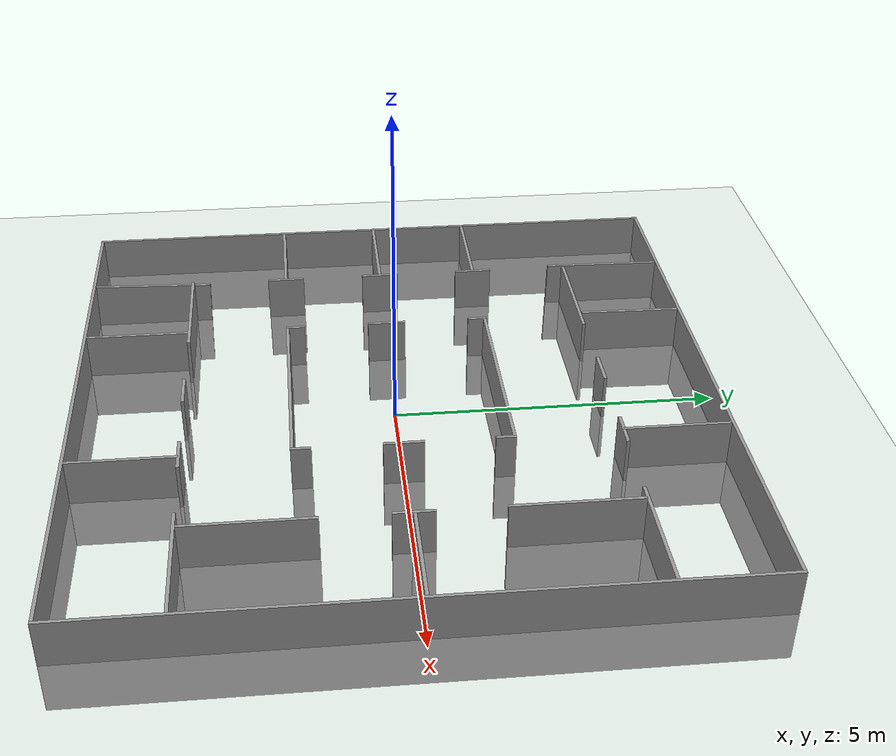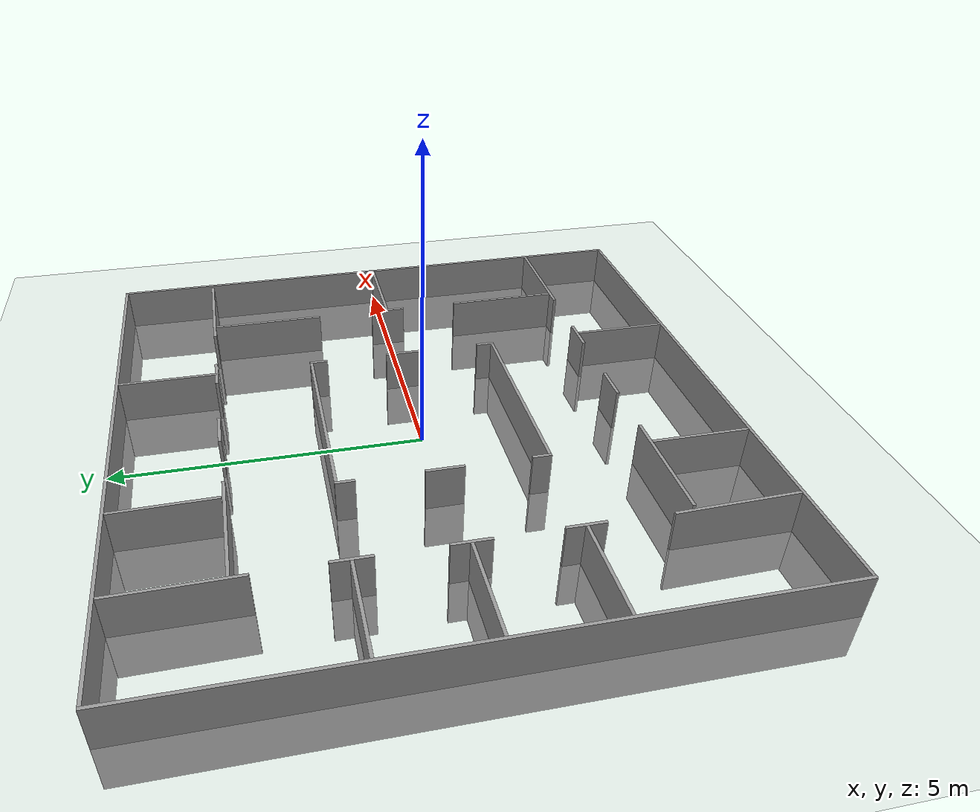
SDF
<?xml version='1.0'?>
<sdf version="1.5">
    <world name="default">
        <!-- A global light source -->
        <include>
            <uri>model://sun</uri>
        </include>
        <!-- A ground plane -->
        <include>
            <uri>model://ground_plane</uri>
        </include>
        <physics type="ode">
        <real_time_update_rate>1000.0</real_time_update_rate>
        <max_step_size>0.001</max_step_size>
        <real_time_factor>1</real_time_factor>
        <ode>
            <solver>
            <type>quick</type>
            <iters>150</iters>
            <precon_iters>0</precon_iters>
            <sor>1.400000</sor>
            <use_dynamic_moi_rescaling>1</use_dynamic_moi_rescaling>
            </solver>
            <constraints>
            <cfm>0.00001</cfm>
            <erp>0.2</erp>
            <contact_max_correcting_vel>2000.000000</contact_max_correcting_vel>
            <contact_surface_layer>0.01000</contact_surface_layer>
            </constraints>
        </ode>
        </physics>
        <!-- Sample object -->
        <include>
            <uri>model://circular_corridor</uri>
            <pose>0 0 0 0 0 0</pose>
        </include>
        <scene>
            <ambient>0.4 0.4 0.4 1</ambient>
            <background>0.7 0.7 0.7 1</background>
            <shadows>true</shadows>
        </scene>
        <gui fullscreen='0'>
            <camera name='user_camera'>
                <pose>0.8 0.0 12.0 0 1.5708 0</pose>
                <view_controller>orbit</view_controller>
            </camera>
        </gui>
    </world>
</sdf>

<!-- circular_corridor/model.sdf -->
<sdf version='1.6'>
  <model name='circular_corridor'>
    <link name='link'>
      <self_collide>0</self_collide>
      <enable_wind>0</enable_wind>
      <kinematic>0</kinematic>
      <pose frame=''>-0 -1.6 -0.05 0 -0 0</pose>
      <gravity>1</gravity>
      <visual name='visual'>
        <geometry>
          <box>
            <size>3.2 0.05 1.5</size>
          </box>
        </geometry>
        <material>
          <script>
            <name>Gazebo/Grey</name>
            <uri>file://media/materials/scripts/gazebo.material</uri>
          </script>
          <shader type='vertex'>
            <normal_map>__default__</normal_map>
          </shader>
          <ambient>0.3 0.3 0.3 1</ambient>
          <diffuse>0.7 0.7 0.7 1</diffuse>
          <specular>0.01 0.01 0.01 1</specular>
          <emissive>0 0 0 1</emissive>
        </material>
        <pose frame=''>0 0 0 0 -0 0</pose>
        <transparency>0</transparency>
        <cast_shadows>1</cast_shadows>
      </visual>
      <collision name='collision'>
        <laser_retro>0</laser_retro>
        <max_contacts>10</max_contacts>
        <pose frame=''>0 0 0 0 -0 0</pose>
        <geometry>
          <box>
            <size>3.2 0.05 1.5</size>
          </box>
        </geometry>
        <surface>
          <friction>
            <ode>
              <mu>1</mu>
              <mu2>1</mu2>
              <fdir1>0 0 0</fdir1>
              <slip1>0</slip1>
              <slip2>0</slip2>
            </ode>
            <torsional>
              <coefficient>1</coefficient>
              <patch_radius>0</patch_radius>
              <surface_radius>0</surface_radius>
              <use_patch_radius>1</use_patch_radius>
              <ode>
                <slip>0</slip>
              </ode>
            </torsional>
          </friction>
          <bounce>
            <restitution_coefficient>0</restitution_coefficient>
            <threshold>1e+06</threshold>
          </bounce>
          <contact>
            <collide_without_contact>0</collide_without_contact>
            <collide_without_contact_bitmask>1</collide_without_contact_bitmask>
            <collide_bitmask>1</collide_bitmask>
            <ode>
              <soft_cfm>0</soft_cfm>
              <soft_erp>0.2</soft_erp>
              <kp>1e+13</kp>
              <kd>1</kd>
              <max_vel>0.01</max_vel>
              <min_depth>0</min_depth>
            </ode>
            <bullet>
              <split_impulse>1</split_impulse>
              <split_impulse_penetration_threshold>-0.01</split_impulse_penetration_threshold>
              <soft_cfm>0</soft_cfm>
              <soft_erp>0.2</soft_erp>
              <kp>1e+13</kp>
              <kd>1</kd>
            </bullet>
          </contact>
        </surface>
      </collision>
    </link>
    <link name='link_0'>
      <pose frame=''>-3.175 -0 -0.05 -0 -0 -1.5708</pose>
      <gravity>1</gravity>
      <self_collide>0</self_collide>
      <kinematic>0</kinematic>
      <enable_wind>0</enable_wind>
      <visual name='visual'>
        <pose frame=''>0 0 0 0 -0 0</pose>
        <geometry>
          <box>
            <size>0.6 0.05 1.5</size>
          </box>
        </geometry>
        <material>
          <lighting>1</lighting>
          <script>
            <uri>file://media/materials/scripts/gazebo.material</uri>
            <name>Gazebo/Grey</name>
          </script>
          <shader type='vertex'>
            <normal_map>__default__</normal_map>
          </shader>
          <ambient>0.3 0.3 0.3 1</ambient>
          <diffuse>0.7 0.7 0.7 1</diffuse>
          <specular>0.01 0.01 0.01 1</specular>
          <emissive>0 0 0 1</emissive>
        </material>
        <transparency>0</transparency>
        <cast_shadows>1</cast_shadows>
      </visual>
      <collision name='collision'>
        <laser_retro>0</laser_retro>
        <max_contacts>10</max_contacts>
        <pose frame=''>0 0 0 0 -0 0</pose>
        <geometry>
          <box>
            <size>0.6 0.05 1.5</size>
          </box>
        </geometry>
        <surface>
          <friction>
            <ode>
              <mu>1</mu>
              <mu2>1</mu2>
              <fdir1>0 0 0</fdir1>
              <slip1>0</slip1>
              <slip2>0</slip2>
            </ode>
            <torsional>
              <coefficient>1</coefficient>
              <patch_radius>0</patch_radius>
              <surface_radius>0</surface_radius>
              <use_patch_radius>1</use_patch_radius>
              <ode>
                <slip>0</slip>
              </ode>
            </torsional>
          </friction>
          <bounce>
            <restitution_coefficient>0</restitution_coefficient>
            <threshold>1e+06</threshold>
          </bounce>
          <contact>
            <collide_without_contact>0</collide_without_contact>
            <collide_without_contact_bitmask>1</collide_without_contact_bitmask>
            <collide_bitmask>1</collide_bitmask>
            <ode>
              <soft_cfm>0</soft_cfm>
              <soft_erp>0.2</soft_erp>
              <kp>1e+13</kp>
              <kd>1</kd>
              <max_vel>0.01</max_vel>
              <min_depth>0</min_depth>
            </ode>
            <bullet>
              <split_impulse>1</split_impulse>
              <split_impulse_penetration_threshold>-0.01</split_impulse_penetration_threshold>
              <soft_cfm>0</soft_cfm>
              <soft_erp>0.2</soft_erp>
              <kp>1e+13</kp>
              <kd>1</kd>
            </bullet>
          </contact>
        </surface>
      </collision>
    </link>
    <link name='link_0_0'>
      <pose frame=''>-2.225 3.175 -0.05 -0 -0 -8e-06</pose>
      <gravity>1</gravity>
      <self_collide>0</self_collide>
      <kinematic>0</kinematic>
      <enable_wind>0</enable_wind>
      <visual name='visual'>
        <pose frame=''>0 0 0 0 -0 0</pose>
        <geometry>
          <box>
            <size>1.9 0.05 1.5</size>
          </box>
        </geometry>
        <material>
          <lighting>1</lighting>
          <script>
            <uri>file://media/materials/scripts/gazebo.material</uri>
            <name>Gazebo/Grey</name>
          </script>
          <shader type='vertex'>
            <normal_map>__default__</normal_map>
          </shader>
          <ambient>0.3 0.3 0.3 1</ambient>
          <diffuse>0.7 0.7 0.7 1</diffuse>
          <specular>0.01 0.01 0.01 1</specular>
          <emissive>0 0 0 1</emissive>
        </material>
        <transparency>0</transparency>
        <cast_shadows>1</cast_shadows>
      </visual>
      <collision name='collision'>
        <laser_retro>0</laser_retro>
        <max_contacts>10</max_contacts>
        <pose frame=''>0 0 0 0 -0 0</pose>
        <geometry>
          <box>
            <size>1.9 0.05 1.5</size>
          </box>
        </geometry>
        <surface>
          <friction>
            <ode>
              <mu>1</mu>
              <mu2>1</mu2>
              <fdir1>0 0 0</fdir1>
              <slip1>0</slip1>
              <slip2>0</slip2>
            </ode>
            <torsional>
              <coefficient>1</coefficient>
              <patch_radius>0</patch_radius>
              <surface_radius>0</surface_radius>
              <use_patch_radius>1</use_patch_radius>
              <ode>
                <slip>0</slip>
              </ode>
            </torsional>
          </friction>
          <bounce>
            <restitution_coefficient>0</restitution_coefficient>
            <threshold>1e+06</threshold>
          </bounce>
          <contact>
            <collide_without_contact>0</collide_without_contact>
            <collide_without_contact_bitmask>1</collide_without_contact_bitmask>
            <collide_bitmask>1</collide_bitmask>
            <ode>
              <soft_cfm>0</soft_cfm>
              <soft_erp>0.2</soft_erp>
              <kp>1e+13</kp>
              <kd>1</kd>
              <max_vel>0.01</max_vel>
              <min_depth>0</min_depth>
            </ode>
            <bullet>
              <split_impulse>1</split_impulse>
              <split_impulse_penetration_threshold>-0.01</split_impulse_penetration_threshold>
              <soft_cfm>0</soft_cfm>
              <soft_erp>0.2</soft_erp>
              <kp>1e+13</kp>
              <kd>1</kd>
            </bullet>
          </contact>
        </surface>
      </collision>
    </link>
    <link name='link_0_0_clone'>
      <pose frame=''>-2.205 -3.175 -0.005508 -0.013849 3.8e-05 -8e-06</pose>
      <gravity>1</gravity>
      <self_collide>0</self_collide>
      <kinematic>0</kinematic>
      <enable_wind>0</enable_wind>
      <visual name='visual'>
        <pose frame=''>0 0 0 0 -0 0</pose>
        <geometry>
          <box>
            <size>1.9 0.05 1.5</size>
          </box>
        </geometry>
        <material>
          <lighting>1</lighting>
          <script>
            <uri>file://media/materials/scripts/gazebo.material</uri>
            <name>Gazebo/Grey</name>
          </script>
          <shader type='vertex'>
            <normal_map>__default__</normal_map>
          </shader>
          <ambient>0.3 0.3 0.3 1</ambient>
          <diffuse>0.7 0.7 0.7 1</diffuse>
          <specular>0.01 0.01 0.01 1</specular>
          <emissive>0 0 0 1</emissive>
        </material>
        <transparency>0</transparency>
        <cast_shadows>1</cast_shadows>
      </visual>
      <collision name='collision'>
        <laser_retro>0</laser_retro>
        <max_contacts>10</max_contacts>
        <pose frame=''>0 0 0 0 -0 0</pose>
        <geometry>
          <box>
            <size>1.9 0.05 1.5</size>
          </box>
        </geometry>
        <surface>
          <friction>
            <ode>
              <mu>1</mu>
              <mu2>1</mu2>
              <fdir1>0 0 0</fdir1>
              <slip1>0</slip1>
              <slip2>0</slip2>
            </ode>
            <torsional>
              <coefficient>1</coefficient>
              <patch_radius>0</patch_radius>
              <surface_radius>0</surface_radius>
              <use_patch_radius>1</use_patch_radius>
              <ode>
                <slip>0</slip>
              </ode>
            </torsional>
          </friction>
          <bounce>
            <restitution_coefficient>0</restitution_coefficient>
            <threshold>1e+06</threshold>
          </bounce>
          <contact>
            <collide_without_contact>0</collide_without_contact>
            <collide_without_contact_bitmask>1</collide_without_contact_bitmask>
            <collide_bitmask>1</collide_bitmask>
            <ode>
              <soft_cfm>0</soft_cfm>
              <soft_erp>0.2</soft_erp>
              <kp>1e+13</kp>
              <kd>1</kd>
              <max_vel>0.01</max_vel>
              <min_depth>0</min_depth>
            </ode>
            <bullet>
              <split_impulse>1</split_impulse>
              <split_impulse_penetration_threshold>-0.01</split_impulse_penetration_threshold>
              <soft_cfm>0</soft_cfm>
              <soft_erp>0.2</soft_erp>
              <kp>1e+13</kp>
              <kd>1</kd>
            </bullet>
          </contact>
        </surface>
      </collision>
    </link>
    <link name='link_0_0_clone_1'>
      <pose frame=''>-4 -0 -0.05 0 -0 0</pose>
      <gravity>1</gravity>
      <self_collide>0</self_collide>
      <kinematic>0</kinematic>
      <enable_wind>0</enable_wind>
      <visual name='visual'>
        <pose frame=''>0 0 0 0 -0 0</pose>
        <geometry>
          <box>
            <size>1.6 0.05 1.5</size>
          </box>
        </geometry>
        <material>
          <lighting>1</lighting>
          <script>
            <uri>file://media/materials/scripts/gazebo.material</uri>
            <name>Gazebo/Grey</name>
          </script>
          <shader type='vertex'>
            <normal_map>__default__</normal_map>
          </shader>
          <ambient>0.3 0.3 0.3 1</ambient>
          <diffuse>0.7 0.7 0.7 1</diffuse>
          <specular>0.01 0.01 0.01 1</specular>
          <emissive>0 0 0 1</emissive>
        </material>
        <transparency>0</transparency>
        <cast_shadows>1</cast_shadows>
      </visual>
      <collision name='collision'>
        <laser_retro>0</laser_retro>
        <max_contacts>10</max_contacts>
        <pose frame=''>0 0 0 0 -0 0</pose>
        <geometry>
          <box>
            <size>1.6 0.05 1.5</size>
          </box>
        </geometry>
        <surface>
          <friction>
            <ode>
              <mu>1</mu>
              <mu2>1</mu2>
              <fdir1>0 0 0</fdir1>
              <slip1>0</slip1>
              <slip2>0</slip2>
            </ode>
            <torsional>
              <coefficient>1</coefficient>
              <patch_radius>0</patch_radius>
              <surface_radius>0</surface_radius>
              <use_patch_radius>1</use_patch_radius>
              <ode>
                <slip>0</slip>
              </ode>
            </torsional>
          </friction>
          <bounce>
            <restitution_coefficient>0</restitution_coefficient>
            <threshold>1e+06</threshold>
          </bounce>
          <contact>
            <collide_without_contact>0</collide_without_contact>
            <collide_without_contact_bitmask>1</collide_without_contact_bitmask>
            <collide_bitmask>1</collide_bitmask>
            <ode>
              <soft_cfm>0</soft_cfm>
              <soft_erp>0.2</soft_erp>
              <kp>1e+13</kp>
              <kd>1</kd>
              <max_vel>0.01</max_vel>
              <min_depth>0</min_depth>
            </ode>
            <bullet>
              <split_impulse>1</split_impulse>
              <split_impulse_penetration_threshold>-0.01</split_impulse_penetration_threshold>
              <soft_cfm>0</soft_cfm>
              <soft_erp>0.2</soft_erp>
              <kp>1e+13</kp>
              <kd>1</kd>
            </bullet>
          </contact>
        </surface>
      </collision>
    </link>
    <link name='link_0_0_clone_1_clone'>
      <pose frame=''>-4 -1.6 -0.05 0 -0 0</pose>
      <gravity>1</gravity>
      <self_collide>0</self_collide>
      <kinematic>0</kinematic>
      <enable_wind>0</enable_wind>
      <visual name='visual'>
        <pose frame=''>0 0 0 0 -0 0</pose>
        <geometry>
          <box>
            <size>1.6 0.05 1.5</size>
          </box>
        </geometry>
        <material>
          <lighting>1</lighting>
          <script>
            <uri>file://media/materials/scripts/gazebo.material</uri>
            <name>Gazebo/Grey</name>
          </script>
          <shader type='vertex'>
            <normal_map>__default__</normal_map>
          </shader>
          <ambient>0.3 0.3 0.3 1</ambient>
          <diffuse>0.7 0.7 0.7 1</diffuse>
          <specular>0.01 0.01 0.01 1</specular>
          <emissive>0 0 0 1</emissive>
        </material>
        <transparency>0</transparency>
        <cast_shadows>1</cast_shadows>
      </visual>
      <collision name='collision'>
        <laser_retro>0</laser_retro>
        <max_contacts>10</max_contacts>
        <pose frame=''>0 0 0 0 -0 0</pose>
        <geometry>
          <box>
            <size>1.6 0.05 1.5</size>
          </box>
        </geometry>
        <surface>
          <friction>
            <ode>
              <mu>1</mu>
              <mu2>1</mu2>
              <fdir1>0 0 0</fdir1>
              <slip1>0</slip1>
              <slip2>0</slip2>
            </ode>
            <torsional>
              <coefficient>1</coefficient>
              <patch_radius>0</patch_radius>
              <surface_radius>0</surface_radius>
              <use_patch_radius>1</use_patch_radius>
              <ode>
                <slip>0</slip>
              </ode>
            </torsional>
          </friction>
          <bounce>
            <restitution_coefficient>0</restitution_coefficient>
            <threshold>1e+06</threshold>
          </bounce>
          <contact>
            <collide_without_contact>0</collide_without_contact>
            <collide_without_contact_bitmask>1</collide_without_contact_bitmask>
            <collide_bitmask>1</collide_bitmask>
            <ode>
              <soft_cfm>0</soft_cfm>
              <soft_erp>0.2</soft_erp>
              <kp>1e+13</kp>
              <kd>1</kd>
              <max_vel>0.01</max_vel>
              <min_depth>0</min_depth>
            </ode>
            <bullet>
              <split_impulse>1</split_impulse>
              <split_impulse_penetration_threshold>-0.01</split_impulse_penetration_threshold>
              <soft_cfm>0</soft_cfm>
              <soft_erp>0.2</soft_erp>
              <kp>1e+13</kp>
              <kd>1</kd>
            </bullet>
          </contact>
        </surface>
      </collision>
    </link>
    <link name='link_0_0_clone_1_clone_0'>
      <pose frame=''>4 -0 -0.05 -0.013849 3.8e-05 0</pose>
      <gravity>1</gravity>
      <self_collide>0</self_collide>
      <kinematic>0</kinematic>
      <enable_wind>0</enable_wind>
      <visual name='visual'>
        <pose frame=''>0 0 0 0 -0 0</pose>
        <geometry>
          <box>
            <size>1.6 0.05 1.5</size>
          </box>
        </geometry>
        <material>
          <lighting>1</lighting>
          <script>
            <uri>file://media/materials/scripts/gazebo.material</uri>
            <name>Gazebo/Grey</name>
          </script>
          <shader type='vertex'>
            <normal_map>__default__</normal_map>
          </shader>
          <ambient>0.3 0.3 0.3 1</ambient>
          <diffuse>0.7 0.7 0.7 1</diffuse>
          <specular>0.01 0.01 0.01 1</specular>
          <emissive>0 0 0 1</emissive>
        </material>
        <transparency>0</transparency>
        <cast_shadows>1</cast_shadows>
      </visual>
      <collision name='collision'>
        <laser_retro>0</laser_retro>
        <max_contacts>10</max_contacts>
        <pose frame=''>0 0 0 0 -0 0</pose>
        <geometry>
          <box>
            <size>1.6 0.05 1.5</size>
          </box>
        </geometry>
        <surface>
          <friction>
            <ode>
              <mu>1</mu>
              <mu2>1</mu2>
              <fdir1>0 0 0</fdir1>
              <slip1>0</slip1>
              <slip2>0</slip2>
            </ode>
            <torsional>
              <coefficient>1</coefficient>
              <patch_radius>0</patch_radius>
              <surface_radius>0</surface_radius>
              <use_patch_radius>1</use_patch_radius>
              <ode>
                <slip>0</slip>
              </ode>
            </torsional>
          </friction>
          <bounce>
            <restitution_coefficient>0</restitution_coefficient>
            <threshold>1e+06</threshold>
          </bounce>
          <contact>
            <collide_without_contact>0</collide_without_contact>
            <collide_without_contact_bitmask>1</collide_without_contact_bitmask>
            <collide_bitmask>1</collide_bitmask>
            <ode>
              <soft_cfm>0</soft_cfm>
              <soft_erp>0.2</soft_erp>
              <kp>1e+13</kp>
              <kd>1</kd>
              <max_vel>0.01</max_vel>
              <min_depth>0</min_depth>
            </ode>
            <bullet>
              <split_impulse>1</split_impulse>
              <split_impulse_penetration_threshold>-0.01</split_impulse_penetration_threshold>
              <soft_cfm>0</soft_cfm>
              <soft_erp>0.2</soft_erp>
              <kp>1e+13</kp>
              <kd>1</kd>
            </bullet>
          </contact>
        </surface>
      </collision>
    </link>
    <link name='link_0_0_clone_1_clone_clone'>
      <pose frame=''>-4 1.6 -0.05 0 -0 0</pose>
      <gravity>1</gravity>
      <self_collide>0</self_collide>
      <kinematic>0</kinematic>
      <enable_wind>0</enable_wind>
      <visual name='visual'>
        <pose frame=''>0 0 0 0 -0 0</pose>
        <geometry>
          <box>
            <size>1.6 0.05 1.5</size>
          </box>
        </geometry>
        <material>
          <lighting>1</lighting>
          <script>
            <uri>file://media/materials/scripts/gazebo.material</uri>
            <name>Gazebo/Grey</name>
          </script>
          <shader type='vertex'>
            <normal_map>__default__</normal_map>
          </shader>
          <ambient>0.3 0.3 0.3 1</ambient>
          <diffuse>0.7 0.7 0.7 1</diffuse>
          <specular>0.01 0.01 0.01 1</specular>
          <emissive>0 0 0 1</emissive>
        </material>
        <transparency>0</transparency>
        <cast_shadows>1</cast_shadows>
      </visual>
      <collision name='collision'>
        <laser_retro>0</laser_retro>
        <max_contacts>10</max_contacts>
        <pose frame=''>0 0 0 0 -0 0</pose>
        <geometry>
          <box>
            <size>1.6 0.05 1.5</size>
          </box>
        </geometry>
        <surface>
          <friction>
            <ode>
              <mu>1</mu>
              <mu2>1</mu2>
              <fdir1>0 0 0</fdir1>
              <slip1>0</slip1>
              <slip2>0</slip2>
            </ode>
            <torsional>
              <coefficient>1</coefficient>
              <patch_radius>0</patch_radius>
              <surface_radius>0</surface_radius>
              <use_patch_radius>1</use_patch_radius>
              <ode>
                <slip>0</slip>
              </ode>
            </torsional>
          </friction>
          <bounce>
            <restitution_coefficient>0</restitution_coefficient>
            <threshold>1e+06</threshold>
          </bounce>
          <contact>
            <collide_without_contact>0</collide_without_contact>
            <collide_without_contact_bitmask>1</collide_without_contact_bitmask>
            <collide_bitmask>1</collide_bitmask>
            <ode>
              <soft_cfm>0</soft_cfm>
              <soft_erp>0.2</soft_erp>
              <kp>1e+13</kp>
              <kd>1</kd>
              <max_vel>0.01</max_vel>
              <min_depth>0</min_depth>
            </ode>
            <bullet>
              <split_impulse>1</split_impulse>
              <split_impulse_penetration_threshold>-0.01</split_impulse_penetration_threshold>
              <soft_cfm>0</soft_cfm>
              <soft_erp>0.2</soft_erp>
              <kp>1e+13</kp>
              <kd>1</kd>
            </bullet>
          </contact>
        </surface>
      </collision>
    </link>
    <link name='link_0_clone'>
      <pose frame=''>3.175 -0 -0.05 0 -0 -1.57081</pose>
      <gravity>1</gravity>
      <self_collide>0</self_collide>
      <kinematic>0</kinematic>
      <enable_wind>0</enable_wind>
      <visual name='visual'>
        <pose frame=''>0 0 0 0 -0 0</pose>
        <geometry>
          <box>
            <size>0.6 0.05 1.5</size>
          </box>
        </geometry>
        <material>
          <lighting>1</lighting>
          <script>
            <uri>file://media/materials/scripts/gazebo.material</uri>
            <name>Gazebo/Grey</name>
          </script>
          <shader type='vertex'>
            <normal_map>__default__</normal_map>
          </shader>
          <ambient>0.3 0.3 0.3 1</ambient>
          <diffuse>0.7 0.7 0.7 1</diffuse>
          <specular>0.01 0.01 0.01 1</specular>
          <emissive>0 0 0 1</emissive>
        </material>
        <transparency>0</transparency>
        <cast_shadows>1</cast_shadows>
      </visual>
      <collision name='collision'>
        <laser_retro>0</laser_retro>
        <max_contacts>10</max_contacts>
        <pose frame=''>0 0 0 0 -0 0</pose>
        <geometry>
          <box>
            <size>0.6 0.05 1.5</size>
          </box>
        </geometry>
        <surface>
          <friction>
            <ode>
              <mu>1</mu>
              <mu2>1</mu2>
              <fdir1>0 0 0</fdir1>
              <slip1>0</slip1>
              <slip2>0</slip2>
            </ode>
            <torsional>
              <coefficient>1</coefficient>
              <patch_radius>0</patch_radius>
              <surface_radius>0</surface_radius>
              <use_patch_radius>1</use_patch_radius>
              <ode>
                <slip>0</slip>
              </ode>
            </torsional>
          </friction>
          <bounce>
            <restitution_coefficient>0</restitution_coefficient>
            <threshold>1e+06</threshold>
          </bounce>
          <contact>
            <collide_without_contact>0</collide_without_contact>
            <collide_without_contact_bitmask>1</collide_without_contact_bitmask>
            <collide_bitmask>1</collide_bitmask>
            <ode>
              <soft_cfm>0</soft_cfm>
              <soft_erp>0.2</soft_erp>
              <kp>1e+13</kp>
              <kd>1</kd>
              <max_vel>0.01</max_vel>
              <min_depth>0</min_depth>
            </ode>
            <bullet>
              <split_impulse>1</split_impulse>
              <split_impulse_penetration_threshold>-0.01</split_impulse_penetration_threshold>
              <soft_cfm>0</soft_cfm>
              <soft_erp>0.2</soft_erp>
              <kp>1e+13</kp>
              <kd>1</kd>
            </bullet>
          </contact>
        </surface>
      </collision>
    </link>
    <link name='link_0_clone_0'>
      <pose frame=''>-3.175 1.6 -0.05 0 -0 -1.57081</pose>
      <gravity>1</gravity>
      <self_collide>0</self_collide>
      <kinematic>0</kinematic>
      <enable_wind>0</enable_wind>
      <visual name='visual'>
        <pose frame=''>0 0 0 0 -0 0</pose>
        <geometry>
          <box>
            <size>0.6 0.05 1.5</size>
          </box>
        </geometry>
        <material>
          <lighting>1</lighting>
          <script>
            <uri>file://media/materials/scripts/gazebo.material</uri>
            <name>Gazebo/Grey</name>
          </script>
          <shader type='vertex'>
            <normal_map>__default__</normal_map>
          </shader>
          <ambient>0.3 0.3 0.3 1</ambient>
          <diffuse>0.7 0.7 0.7 1</diffuse>
          <specular>0.01 0.01 0.01 1</specular>
          <emissive>0 0 0 1</emissive>
        </material>
        <transparency>0</transparency>
        <cast_shadows>1</cast_shadows>
      </visual>
      <collision name='collision'>
        <laser_retro>0</laser_retro>
        <max_contacts>10</max_contacts>
        <pose frame=''>0 0 0 0 -0 0</pose>
        <geometry>
          <box>
            <size>0.6 0.05 1.5</size>
          </box>
        </geometry>
        <surface>
          <friction>
            <ode>
              <mu>1</mu>
              <mu2>1</mu2>
              <fdir1>0 0 0</fdir1>
              <slip1>0</slip1>
              <slip2>0</slip2>
            </ode>
            <torsional>
              <coefficient>1</coefficient>
              <patch_radius>0</patch_radius>
              <surface_radius>0</surface_radius>
              <use_patch_radius>1</use_patch_radius>
              <ode>
                <slip>0</slip>
              </ode>
            </torsional>
          </friction>
          <bounce>
            <restitution_coefficient>0</restitution_coefficient>
            <threshold>1e+06</threshold>
          </bounce>
          <contact>
            <collide_without_contact>0</collide_without_contact>
            <collide_without_contact_bitmask>1</collide_without_contact_bitmask>
            <collide_bitmask>1</collide_bitmask>
            <ode>
              <soft_cfm>0</soft_cfm>
              <soft_erp>0.2</soft_erp>
              <kp>1e+13</kp>
              <kd>1</kd>
              <max_vel>0.01</max_vel>
              <min_depth>0</min_depth>
            </ode>
            <bullet>
              <split_impulse>1</split_impulse>
              <split_impulse_penetration_threshold>-0.01</split_impulse_penetration_threshold>
              <soft_cfm>0</soft_cfm>
              <soft_erp>0.2</soft_erp>
              <kp>1e+13</kp>
              <kd>1</kd>
            </bullet>
          </contact>
        </surface>
      </collision>
    </link>
    <link name='link_0_clone_0_clone'>
      <pose frame=''>-3.2 3.85 -0.05 -0.000127 -0.013839 -1.57081</pose>
      <gravity>1</gravity>
      <self_collide>0</self_collide>
      <kinematic>0</kinematic>
      <enable_wind>0</enable_wind>
      <visual name='visual'>
        <pose frame=''>0 0 0 0 -0 0</pose>
        <geometry>
          <box>
            <size>1.9 0.05 1.5</size>
          </box>
        </geometry>
        <material>
          <lighting>1</lighting>
          <script>
            <uri>file://media/materials/scripts/gazebo.material</uri>
            <name>Gazebo/Grey</name>
          </script>
          <shader type='vertex'>
            <normal_map>__default__</normal_map>
          </shader>
          <ambient>0.3 0.3 0.3 1</ambient>
          <diffuse>0.7 0.7 0.7 1</diffuse>
          <specular>0.01 0.01 0.01 1</specular>
          <emissive>0 0 0 1</emissive>
        </material>
        <transparency>0</transparency>
        <cast_shadows>1</cast_shadows>
      </visual>
      <collision name='collision'>
        <laser_retro>0</laser_retro>
        <max_contacts>10</max_contacts>
        <pose frame=''>0 0 0 0 -0 0</pose>
        <geometry>
          <box>
            <size>1.9 0.05 1.5</size>
          </box>
        </geometry>
        <surface>
          <friction>
            <ode>
              <mu>1</mu>
              <mu2>1</mu2>
              <fdir1>0 0 0</fdir1>
              <slip1>0</slip1>
              <slip2>0</slip2>
            </ode>
            <torsional>
              <coefficient>1</coefficient>
              <patch_radius>0</patch_radius>
              <surface_radius>0</surface_radius>
              <use_patch_radius>1</use_patch_radius>
              <ode>
                <slip>0</slip>
              </ode>
            </torsional>
          </friction>
          <bounce>
            <restitution_coefficient>0</restitution_coefficient>
            <threshold>1e+06</threshold>
          </bounce>
          <contact>
            <collide_without_contact>0</collide_without_contact>
            <collide_without_contact_bitmask>1</collide_without_contact_bitmask>
            <collide_bitmask>1</collide_bitmask>
            <ode>
              <soft_cfm>0</soft_cfm>
              <soft_erp>0.2</soft_erp>
              <kp>1e+13</kp>
              <kd>1</kd>
              <max_vel>0.01</max_vel>
              <min_depth>0</min_depth>
            </ode>
            <bullet>
              <split_impulse>1</split_impulse>
              <split_impulse_penetration_threshold>-0.01</split_impulse_penetration_threshold>
              <soft_cfm>0</soft_cfm>
              <soft_erp>0.2</soft_erp>
              <kp>1e+13</kp>
              <kd>1</kd>
            </bullet>
          </contact>
        </surface>
      </collision>
    </link>
    <link name='link_0_clone_0_clone_clone'>
      <pose frame=''>-3.175 -3.85 -0.05 -0.000166 -0.027688 -1.57078</pose>
      <gravity>1</gravity>
      <self_collide>0</self_collide>
      <kinematic>0</kinematic>
      <enable_wind>0</enable_wind>
      <visual name='visual'>
        <pose frame=''>0 0 0 0 -0 0</pose>
        <geometry>
          <box>
            <size>1.9 0.05 1.5</size>
          </box>
        </geometry>
        <material>
          <lighting>1</lighting>
          <script>
            <uri>file://media/materials/scripts/gazebo.material</uri>
            <name>Gazebo/Grey</name>
          </script>
          <shader type='vertex'>
            <normal_map>__default__</normal_map>
          </shader>
          <ambient>0.3 0.3 0.3 1</ambient>
          <diffuse>0.7 0.7 0.7 1</diffuse>
          <specular>0.01 0.01 0.01 1</specular>
          <emissive>0 0 0 1</emissive>
        </material>
        <transparency>0</transparency>
        <cast_shadows>1</cast_shadows>
      </visual>
      <collision name='collision'>
        <laser_retro>0</laser_retro>
        <max_contacts>10</max_contacts>
        <pose frame=''>0 0 0 0 -0 0</pose>
        <geometry>
          <box>
            <size>1.9 0.05 1.5</size>
          </box>
        </geometry>
        <surface>
          <friction>
            <ode>
              <mu>1</mu>
              <mu2>1</mu2>
              <fdir1>0 0 0</fdir1>
              <slip1>0</slip1>
              <slip2>0</slip2>
            </ode>
            <torsional>
              <coefficient>1</coefficient>
              <patch_radius>0</patch_radius>
              <surface_radius>0</surface_radius>
              <use_patch_radius>1</use_patch_radius>
              <ode>
                <slip>0</slip>
              </ode>
            </torsional>
          </friction>
          <bounce>
            <restitution_coefficient>0</restitution_coefficient>
            <threshold>1e+06</threshold>
          </bounce>
          <contact>
            <collide_without_contact>0</collide_without_contact>
            <collide_without_contact_bitmask>1</collide_without_contact_bitmask>
            <collide_bitmask>1</collide_bitmask>
            <ode>
              <soft_cfm>0</soft_cfm>
              <soft_erp>0.2</soft_erp>
              <kp>1e+13</kp>
              <kd>1</kd>
              <max_vel>0.01</max_vel>
              <min_depth>0</min_depth>
            </ode>
            <bullet>
              <split_impulse>1</split_impulse>
              <split_impulse_penetration_threshold>-0.01</split_impulse_penetration_threshold>
              <soft_cfm>0</soft_cfm>
              <soft_erp>0.2</soft_erp>
              <kp>1e+13</kp>
              <kd>1</kd>
            </bullet>
          </contact>
        </surface>
      </collision>
    </link>
    <link name='link_0_clone_0_clone_clone_0'>
      <pose frame=''>3.85 3.2 -0.084552 0 0 -3.14158</pose>
      <gravity>1</gravity>
      <self_collide>0</self_collide>
      <kinematic>0</kinematic>
      <enable_wind>0</enable_wind>
      <visual name='visual'>
        <pose frame=''>0 0 0 0 -0 0</pose>
        <geometry>
          <box>
            <size>1.9 0.05 1.5</size>
          </box>
        </geometry>
        <material>
          <lighting>1</lighting>
          <script>
            <uri>file://media/materials/scripts/gazebo.material</uri>
            <name>Gazebo/Grey</name>
          </script>
          <shader type='vertex'>
            <normal_map>__default__</normal_map>
          </shader>
          <ambient>0.3 0.3 0.3 1</ambient>
          <diffuse>0.7 0.7 0.7 1</diffuse>
          <specular>0.01 0.01 0.01 1</specular>
          <emissive>0 0 0 1</emissive>
        </material>
        <transparency>0</transparency>
        <cast_shadows>1</cast_shadows>
      </visual>
      <collision name='collision'>
        <laser_retro>0</laser_retro>
        <max_contacts>10</max_contacts>
        <pose frame=''>0 0 0 0 -0 0</pose>
        <geometry>
          <box>
            <size>1.9 0.05 1.5</size>
          </box>
        </geometry>
        <surface>
          <friction>
            <ode>
              <mu>1</mu>
              <mu2>1</mu2>
              <fdir1>0 0 0</fdir1>
              <slip1>0</slip1>
              <slip2>0</slip2>
            </ode>
            <torsional>
              <coefficient>1</coefficient>
              <patch_radius>0</patch_radius>
              <surface_radius>0</surface_radius>
              <use_patch_radius>1</use_patch_radius>
              <ode>
                <slip>0</slip>
              </ode>
            </torsional>
          </friction>
          <bounce>
            <restitution_coefficient>0</restitution_coefficient>
            <threshold>1e+06</threshold>
          </bounce>
          <contact>
            <collide_without_contact>0</collide_without_contact>
            <collide_without_contact_bitmask>1</collide_without_contact_bitmask>
            <collide_bitmask>1</collide_bitmask>
            <ode>
              <soft_cfm>0</soft_cfm>
              <soft_erp>0.2</soft_erp>
              <kp>1e+13</kp>
              <kd>1</kd>
              <max_vel>0.01</max_vel>
              <min_depth>0</min_depth>
            </ode>
            <bullet>
              <split_impulse>1</split_impulse>
              <split_impulse_penetration_threshold>-0.01</split_impulse_penetration_threshold>
              <soft_cfm>0</soft_cfm>
              <soft_erp>0.2</soft_erp>
              <kp>1e+13</kp>
              <kd>1</kd>
            </bullet>
          </contact>
        </surface>
      </collision>
    </link>
    <link name='link_0_clone_0_clone_clone_1'>
      <pose frame=''>3.85 -3.2 -0.05 0 -0 8e-06</pose>
      <gravity>1</gravity>
      <self_collide>0</self_collide>
      <kinematic>0</kinematic>
      <enable_wind>0</enable_wind>
      <visual name='visual'>
        <pose frame=''>0 0 0 0 -0 0</pose>
        <geometry>
          <box>
            <size>1.9 0.05 1.5</size>
          </box>
        </geometry>
        <material>
          <lighting>1</lighting>
          <script>
            <uri>file://media/materials/scripts/gazebo.material</uri>
            <name>Gazebo/Grey</name>
          </script>
          <shader type='vertex'>
            <normal_map>__default__</normal_map>
          </shader>
          <ambient>0.3 0.3 0.3 1</ambient>
          <diffuse>0.7 0.7 0.7 1</diffuse>
          <specular>0.01 0.01 0.01 1</specular>
          <emissive>0 0 0 1</emissive>
        </material>
        <transparency>0</transparency>
        <cast_shadows>1</cast_shadows>
      </visual>
      <collision name='collision'>
        <laser_retro>0</laser_retro>
        <max_contacts>10</max_contacts>
        <pose frame=''>0 0 0 0 -0 0</pose>
        <geometry>
          <box>
            <size>1.9 0.05 1.5</size>
          </box>
        </geometry>
        <surface>
          <friction>
            <ode>
              <mu>1</mu>
              <mu2>1</mu2>
              <fdir1>0 0 0</fdir1>
              <slip1>0</slip1>
              <slip2>0</slip2>
            </ode>
            <torsional>
              <coefficient>1</coefficient>
              <patch_radius>0</patch_radius>
              <surface_radius>0</surface_radius>
              <use_patch_radius>1</use_patch_radius>
              <ode>
                <slip>0</slip>
              </ode>
            </torsional>
          </friction>
          <bounce>
            <restitution_coefficient>0</restitution_coefficient>
            <threshold>1e+06</threshold>
          </bounce>
          <contact>
            <collide_without_contact>0</collide_without_contact>
            <collide_without_contact_bitmask>1</collide_without_contact_bitmask>
            <collide_bitmask>1</collide_bitmask>
            <ode>
              <soft_cfm>0</soft_cfm>
              <soft_erp>0.2</soft_erp>
              <kp>1e+13</kp>
              <kd>1</kd>
              <max_vel>0.01</max_vel>
              <min_depth>0</min_depth>
            </ode>
            <bullet>
              <split_impulse>1</split_impulse>
              <split_impulse_penetration_threshold>-0.01</split_impulse_penetration_threshold>
              <soft_cfm>0</soft_cfm>
              <soft_erp>0.2</soft_erp>
              <kp>1e+13</kp>
              <kd>1</kd>
            </bullet>
          </contact>
        </surface>
      </collision>
    </link>
    <link name='link_0_clone_1'>
      <pose frame=''>-3.175 -1.6 -0.05 0 -0 -1.57081</pose>
      <gravity>1</gravity>
      <self_collide>0</self_collide>
      <kinematic>0</kinematic>
      <enable_wind>0</enable_wind>
      <visual name='visual'>
        <pose frame=''>0 0 0 0 -0 0</pose>
        <geometry>
          <box>
            <size>0.6 0.05 1.5</size>
          </box>
        </geometry>
        <material>
          <lighting>1</lighting>
          <script>
            <uri>file://media/materials/scripts/gazebo.material</uri>
            <name>Gazebo/Grey</name>
          </script>
          <shader type='vertex'>
            <normal_map>__default__</normal_map>
          </shader>
          <ambient>0.3 0.3 0.3 1</ambient>
          <diffuse>0.7 0.7 0.7 1</diffuse>
          <specular>0.01 0.01 0.01 1</specular>
          <emissive>0 0 0 1</emissive>
        </material>
        <transparency>0</transparency>
        <cast_shadows>1</cast_shadows>
      </visual>
      <collision name='collision'>
        <laser_retro>0</laser_retro>
        <max_contacts>10</max_contacts>
        <pose frame=''>0 0 0 0 -0 0</pose>
        <geometry>
          <box>
            <size>0.6 0.05 1.5</size>
          </box>
        </geometry>
        <surface>
          <friction>
            <ode>
              <mu>1</mu>
              <mu2>1</mu2>
              <fdir1>0 0 0</fdir1>
              <slip1>0</slip1>
              <slip2>0</slip2>
            </ode>
            <torsional>
              <coefficient>1</coefficient>
              <patch_radius>0</patch_radius>
              <surface_radius>0</surface_radius>
              <use_patch_radius>1</use_patch_radius>
              <ode>
                <slip>0</slip>
              </ode>
            </torsional>
          </friction>
          <bounce>
            <restitution_coefficient>0</restitution_coefficient>
            <threshold>1e+06</threshold>
          </bounce>
          <contact>
            <collide_without_contact>0</collide_without_contact>
            <collide_without_contact_bitmask>1</collide_without_contact_bitmask>
            <collide_bitmask>1</collide_bitmask>
            <ode>
              <soft_cfm>0</soft_cfm>
              <soft_erp>0.2</soft_erp>
              <kp>1e+13</kp>
              <kd>1</kd>
              <max_vel>0.01</max_vel>
              <min_depth>0</min_depth>
            </ode>
            <bullet>
              <split_impulse>1</split_impulse>
              <split_impulse_penetration_threshold>-0.01</split_impulse_penetration_threshold>
              <soft_cfm>0</soft_cfm>
              <soft_erp>0.2</soft_erp>
              <kp>1e+13</kp>
              <kd>1</kd>
            </bullet>
          </contact>
        </surface>
      </collision>
    </link>
    <link name='link_0_clone_2'>
      <pose frame=''>-0 -3.2 -0.05 1e-05 8.9e-05 -1.4e-05</pose>
      <gravity>1</gravity>
      <self_collide>0</self_collide>
      <kinematic>0</kinematic>
      <enable_wind>0</enable_wind>
      <visual name='visual'>
        <pose frame=''>0 0 0 0 -0 0</pose>
        <geometry>
          <box>
            <size>0.6 0.05 1.5</size>
          </box>
        </geometry>
        <material>
          <lighting>1</lighting>
          <script>
            <uri>file://media/materials/scripts/gazebo.material</uri>
            <name>Gazebo/Grey</name>
          </script>
          <shader type='vertex'>
            <normal_map>__default__</normal_map>
          </shader>
          <ambient>0.3 0.3 0.3 1</ambient>
          <diffuse>0.7 0.7 0.7 1</diffuse>
          <specular>0.01 0.01 0.01 1</specular>
          <emissive>0 0 0 1</emissive>
        </material>
        <transparency>0</transparency>
        <cast_shadows>1</cast_shadows>
      </visual>
      <collision name='collision'>
        <laser_retro>0</laser_retro>
        <max_contacts>10</max_contacts>
        <pose frame=''>0 0 0 0 -0 0</pose>
        <geometry>
          <box>
            <size>0.6 0.05 1.5</size>
          </box>
        </geometry>
        <surface>
          <friction>
            <ode>
              <mu>1</mu>
              <mu2>1</mu2>
              <fdir1>0 0 0</fdir1>
              <slip1>0</slip1>
              <slip2>0</slip2>
            </ode>
            <torsional>
              <coefficient>1</coefficient>
              <patch_radius>0</patch_radius>
              <surface_radius>0</surface_radius>
              <use_patch_radius>1</use_patch_radius>
              <ode>
                <slip>0</slip>
              </ode>
            </torsional>
          </friction>
          <bounce>
            <restitution_coefficient>0</restitution_coefficient>
            <threshold>1e+06</threshold>
          </bounce>
          <contact>
            <collide_without_contact>0</collide_without_contact>
            <collide_without_contact_bitmask>1</collide_without_contact_bitmask>
            <collide_bitmask>1</collide_bitmask>
            <ode>
              <soft_cfm>0</soft_cfm>
              <soft_erp>0.2</soft_erp>
              <kp>1e+13</kp>
              <kd>1</kd>
              <max_vel>0.01</max_vel>
              <min_depth>0</min_depth>
            </ode>
            <bullet>
              <split_impulse>1</split_impulse>
              <split_impulse_penetration_threshold>-0.01</split_impulse_penetration_threshold>
              <soft_cfm>0</soft_cfm>
              <soft_erp>0.2</soft_erp>
              <kp>1e+13</kp>
              <kd>1</kd>
            </bullet>
          </contact>
        </surface>
      </collision>
    </link>
    <link name='link_0_clone_2_clone'>
      <pose frame=''>0 3.2 -0.05 1e-05 0.000178 -2.2e-05</pose>
      <gravity>1</gravity>
      <self_collide>0</self_collide>
      <kinematic>0</kinematic>
      <enable_wind>0</enable_wind>
      <visual name='visual'>
        <pose frame=''>0 0 0 0 -0 0</pose>
        <geometry>
          <box>
            <size>0.6 0.05 1.5</size>
          </box>
        </geometry>
        <material>
          <lighting>1</lighting>
          <script>
            <uri>file://media/materials/scripts/gazebo.material</uri>
            <name>Gazebo/Grey</name>
          </script>
          <shader type='vertex'>
            <normal_map>__default__</normal_map>
          </shader>
          <ambient>0.3 0.3 0.3 1</ambient>
          <diffuse>0.7 0.7 0.7 1</diffuse>
          <specular>0.01 0.01 0.01 1</specular>
          <emissive>0 0 0 1</emissive>
        </material>
        <transparency>0</transparency>
        <cast_shadows>1</cast_shadows>
      </visual>
      <collision name='collision'>
        <laser_retro>0</laser_retro>
        <max_contacts>10</max_contacts>
        <pose frame=''>0 0 0 0 -0 0</pose>
        <geometry>
          <box>
            <size>0.6 0.05 1.5</size>
          </box>
        </geometry>
        <surface>
          <friction>
            <ode>
              <mu>1</mu>
              <mu2>1</mu2>
              <fdir1>0 0 0</fdir1>
              <slip1>0</slip1>
              <slip2>0</slip2>
            </ode>
            <torsional>
              <coefficient>1</coefficient>
              <patch_radius>0</patch_radius>
              <surface_radius>0</surface_radius>
              <use_patch_radius>1</use_patch_radius>
              <ode>
                <slip>0</slip>
              </ode>
            </torsional>
          </friction>
          <bounce>
            <restitution_coefficient>0</restitution_coefficient>
            <threshold>1e+06</threshold>
          </bounce>
          <contact>
            <collide_without_contact>0</collide_without_contact>
            <collide_without_contact_bitmask>1</collide_without_contact_bitmask>
            <collide_bitmask>1</collide_bitmask>
            <ode>
              <soft_cfm>0</soft_cfm>
              <soft_erp>0.2</soft_erp>
              <kp>1e+13</kp>
              <kd>1</kd>
              <max_vel>0.01</max_vel>
              <min_depth>0</min_depth>
            </ode>
            <bullet>
              <split_impulse>1</split_impulse>
              <split_impulse_penetration_threshold>-0.01</split_impulse_penetration_threshold>
              <soft_cfm>0</soft_cfm>
              <soft_erp>0.2</soft_erp>
              <kp>1e+13</kp>
              <kd>1</kd>
            </bullet>
          </contact>
        </surface>
      </collision>
    </link>
    <link name='link_0_clone_2_clone_0'>
      <pose frame=''>1.6 -3.2 -0.05 0 0 -2.2e-05</pose>
      <gravity>1</gravity>
      <self_collide>0</self_collide>
      <kinematic>0</kinematic>
      <enable_wind>0</enable_wind>
      <visual name='visual'>
        <pose frame=''>0 0 0 0 -0 0</pose>
        <geometry>
          <box>
            <size>0.6 0.05 1.5</size>
          </box>
        </geometry>
        <material>
          <lighting>1</lighting>
          <script>
            <uri>file://media/materials/scripts/gazebo.material</uri>
            <name>Gazebo/Grey</name>
          </script>
          <shader type='vertex'>
            <normal_map>__default__</normal_map>
          </shader>
          <ambient>0.3 0.3 0.3 1</ambient>
          <diffuse>0.7 0.7 0.7 1</diffuse>
          <specular>0.01 0.01 0.01 1</specular>
          <emissive>0 0 0 1</emissive>
        </material>
        <transparency>0</transparency>
        <cast_shadows>1</cast_shadows>
      </visual>
      <collision name='collision'>
        <laser_retro>0</laser_retro>
        <max_contacts>10</max_contacts>
        <pose frame=''>0 0 0 0 -0 0</pose>
        <geometry>
          <box>
            <size>0.6 0.05 1.5</size>
          </box>
        </geometry>
        <surface>
          <friction>
            <ode>
              <mu>1</mu>
              <mu2>1</mu2>
              <fdir1>0 0 0</fdir1>
              <slip1>0</slip1>
              <slip2>0</slip2>
            </ode>
            <torsional>
              <coefficient>1</coefficient>
              <patch_radius>0</patch_radius>
              <surface_radius>0</surface_radius>
              <use_patch_radius>1</use_patch_radius>
              <ode>
                <slip>0</slip>
              </ode>
            </torsional>
          </friction>
          <bounce>
            <restitution_coefficient>0</restitution_coefficient>
            <threshold>1e+06</threshold>
          </bounce>
          <contact>
            <collide_without_contact>0</collide_without_contact>
            <collide_without_contact_bitmask>1</collide_without_contact_bitmask>
            <collide_bitmask>1</collide_bitmask>
            <ode>
              <soft_cfm>0</soft_cfm>
              <soft_erp>0.2</soft_erp>
              <kp>1e+13</kp>
              <kd>1</kd>
              <max_vel>0.01</max_vel>
              <min_depth>0</min_depth>
            </ode>
            <bullet>
              <split_impulse>1</split_impulse>
              <split_impulse_penetration_threshold>-0.01</split_impulse_penetration_threshold>
              <soft_cfm>0</soft_cfm>
              <soft_erp>0.2</soft_erp>
              <kp>1e+13</kp>
              <kd>1</kd>
            </bullet>
          </contact>
        </surface>
      </collision>
    </link>
    <link name='link_0_clone_2_clone_clone'>
      <pose frame=''>1.6 3.2 -0.05 0 -0 -3e-05</pose>
      <gravity>1</gravity>
      <self_collide>0</self_collide>
      <kinematic>0</kinematic>
      <enable_wind>0</enable_wind>
      <visual name='visual'>
        <pose frame=''>0 0 0 0 -0 0</pose>
        <geometry>
          <box>
            <size>0.6 0.05 1.5</size>
          </box>
        </geometry>
        <material>
          <lighting>1</lighting>
          <script>
            <uri>file://media/materials/scripts/gazebo.material</uri>
            <name>Gazebo/Grey</name>
          </script>
          <shader type='vertex'>
            <normal_map>__default__</normal_map>
          </shader>
          <ambient>0.3 0.3 0.3 1</ambient>
          <diffuse>0.7 0.7 0.7 1</diffuse>
          <specular>0.01 0.01 0.01 1</specular>
          <emissive>0 0 0 1</emissive>
        </material>
        <transparency>0</transparency>
        <cast_shadows>1</cast_shadows>
      </visual>
      <collision name='collision'>
        <laser_retro>0</laser_retro>
        <max_contacts>10</max_contacts>
        <pose frame=''>0 0 0 0 -0 0</pose>
        <geometry>
          <box>
            <size>0.6 0.05 1.5</size>
          </box>
        </geometry>
        <surface>
          <friction>
            <ode>
              <mu>1</mu>
              <mu2>1</mu2>
              <fdir1>0 0 0</fdir1>
              <slip1>0</slip1>
              <slip2>0</slip2>
            </ode>
            <torsional>
              <coefficient>1</coefficient>
              <patch_radius>0</patch_radius>
              <surface_radius>0</surface_radius>
              <use_patch_radius>1</use_patch_radius>
              <ode>
                <slip>0</slip>
              </ode>
            </torsional>
          </friction>
          <bounce>
            <restitution_coefficient>0</restitution_coefficient>
            <threshold>1e+06</threshold>
          </bounce>
          <contact>
            <collide_without_contact>0</collide_without_contact>
            <collide_without_contact_bitmask>1</collide_without_contact_bitmask>
            <collide_bitmask>1</collide_bitmask>
            <ode>
              <soft_cfm>0</soft_cfm>
              <soft_erp>0.2</soft_erp>
              <kp>1e+13</kp>
              <kd>1</kd>
              <max_vel>0.01</max_vel>
              <min_depth>0</min_depth>
            </ode>
            <bullet>
              <split_impulse>1</split_impulse>
              <split_impulse_penetration_threshold>-0.01</split_impulse_penetration_threshold>
              <soft_cfm>0</soft_cfm>
              <soft_erp>0.2</soft_erp>
              <kp>1e+13</kp>
              <kd>1</kd>
            </bullet>
          </contact>
        </surface>
      </collision>
    </link>
    <link name='link_0_clone_clone'>
      <pose frame=''>3.175 2.225 -0.05 0 0 -1.57082</pose>
      <gravity>1</gravity>
      <self_collide>0</self_collide>
      <kinematic>0</kinematic>
      <enable_wind>0</enable_wind>
      <visual name='visual'>
        <pose frame=''>0 0 0 0 -0 0</pose>
        <geometry>
          <box>
            <size>1.9 0.05 1.5</size>
          </box>
        </geometry>
        <material>
          <lighting>1</lighting>
          <script>
            <uri>file://media/materials/scripts/gazebo.material</uri>
            <name>Gazebo/Grey</name>
          </script>
          <shader type='vertex'>
            <normal_map>__default__</normal_map>
          </shader>
          <ambient>0.3 0.3 0.3 1</ambient>
          <diffuse>0.7 0.7 0.7 1</diffuse>
          <specular>0.01 0.01 0.01 1</specular>
          <emissive>0 0 0 1</emissive>
        </material>
        <transparency>0</transparency>
        <cast_shadows>1</cast_shadows>
      </visual>
      <collision name='collision'>
        <laser_retro>0</laser_retro>
        <max_contacts>10</max_contacts>
        <pose frame=''>0 0 0 0 -0 0</pose>
        <geometry>
          <box>
            <size>1.9 0.05 1.5</size>
          </box>
        </geometry>
        <surface>
          <friction>
            <ode>
              <mu>1</mu>
              <mu2>1</mu2>
              <fdir1>0 0 0</fdir1>
              <slip1>0</slip1>
              <slip2>0</slip2>
            </ode>
            <torsional>
              <coefficient>1</coefficient>
              <patch_radius>0</patch_radius>
              <surface_radius>0</surface_radius>
              <use_patch_radius>1</use_patch_radius>
              <ode>
                <slip>0</slip>
              </ode>
            </torsional>
          </friction>
          <bounce>
            <restitution_coefficient>0</restitution_coefficient>
            <threshold>1e+06</threshold>
          </bounce>
          <contact>
            <collide_without_contact>0</collide_without_contact>
            <collide_without_contact_bitmask>1</collide_without_contact_bitmask>
            <collide_bitmask>1</collide_bitmask>
            <ode>
              <soft_cfm>0</soft_cfm>
              <soft_erp>0.2</soft_erp>
              <kp>1e+13</kp>
              <kd>1</kd>
              <max_vel>0.01</max_vel>
              <min_depth>0</min_depth>
            </ode>
            <bullet>
              <split_impulse>1</split_impulse>
              <split_impulse_penetration_threshold>-0.01</split_impulse_penetration_threshold>
              <soft_cfm>0</soft_cfm>
              <soft_erp>0.2</soft_erp>
              <kp>1e+13</kp>
              <kd>1</kd>
            </bullet>
          </contact>
        </surface>
      </collision>
    </link>
    <link name='link_0_clone_clone_0'>
      <pose frame=''>3.175 -2.225 -0.050008 0 -0 -1.57083</pose>
      <gravity>1</gravity>
      <self_collide>0</self_collide>
      <kinematic>0</kinematic>
      <enable_wind>0</enable_wind>
      <visual name='visual'>
        <pose frame=''>0 0 0 0 -0 0</pose>
        <geometry>
          <box>
            <size>1.9 0.05 1.5</size>
          </box>
        </geometry>
        <material>
          <lighting>1</lighting>
          <script>
            <uri>file://media/materials/scripts/gazebo.material</uri>
            <name>Gazebo/Grey</name>
          </script>
          <shader type='vertex'>
            <normal_map>__default__</normal_map>
          </shader>
          <ambient>0.3 0.3 0.3 1</ambient>
          <diffuse>0.7 0.7 0.7 1</diffuse>
          <specular>0.01 0.01 0.01 1</specular>
          <emissive>0 0 0 1</emissive>
        </material>
        <transparency>0</transparency>
        <cast_shadows>1</cast_shadows>
      </visual>
      <collision name='collision'>
        <laser_retro>0</laser_retro>
        <max_contacts>10</max_contacts>
        <pose frame=''>0 0 0 0 -0 0</pose>
        <geometry>
          <box>
            <size>1.9 0.05 1.5</size>
          </box>
        </geometry>
        <surface>
          <friction>
            <ode>
              <mu>1</mu>
              <mu2>1</mu2>
              <fdir1>0 0 0</fdir1>
              <slip1>0</slip1>
              <slip2>0</slip2>
            </ode>
            <torsional>
              <coefficient>1</coefficient>
              <patch_radius>0</patch_radius>
              <surface_radius>0</surface_radius>
              <use_patch_radius>1</use_patch_radius>
              <ode>
                <slip>0</slip>
              </ode>
            </torsional>
          </friction>
          <bounce>
            <restitution_coefficient>0</restitution_coefficient>
            <threshold>1e+06</threshold>
          </bounce>
          <contact>
            <collide_without_contact>0</collide_without_contact>
            <collide_without_contact_bitmask>1</collide_without_contact_bitmask>
            <collide_bitmask>1</collide_bitmask>
            <ode>
              <soft_cfm>0</soft_cfm>
              <soft_erp>0.2</soft_erp>
              <kp>1e+13</kp>
              <kd>1</kd>
              <max_vel>0.01</max_vel>
              <min_depth>0</min_depth>
            </ode>
            <bullet>
              <split_impulse>1</split_impulse>
              <split_impulse_penetration_threshold>-0.01</split_impulse_penetration_threshold>
              <soft_cfm>0</soft_cfm>
              <soft_erp>0.2</soft_erp>
              <kp>1e+13</kp>
              <kd>1</kd>
            </bullet>
          </contact>
        </surface>
      </collision>
    </link>
    <link name='link_clone'>
      <self_collide>0</self_collide>
      <enable_wind>0</enable_wind>
      <kinematic>0</kinematic>
      <pose frame=''>0 1.6 -0.05 0 -0 0</pose>
      <gravity>1</gravity>
      <visual name='visual'>
        <geometry>
          <box>
            <size>3.2 0.05 1.5</size>
          </box>
        </geometry>
        <material>
          <script>
            <name>Gazebo/Grey</name>
            <uri>file://media/materials/scripts/gazebo.material</uri>
          </script>
          <shader type='vertex'>
            <normal_map>__default__</normal_map>
          </shader>
          <ambient>0.3 0.3 0.3 1</ambient>
          <diffuse>0.7 0.7 0.7 1</diffuse>
          <specular>0.01 0.01 0.01 1</specular>
          <emissive>0 0 0 1</emissive>
        </material>
        <pose frame=''>0 0 0 0 -0 0</pose>
        <transparency>0</transparency>
        <cast_shadows>1</cast_shadows>
      </visual>
      <collision name='collision'>
        <laser_retro>0</laser_retro>
        <max_contacts>10</max_contacts>
        <pose frame=''>0 0 0 0 -0 0</pose>
        <geometry>
          <box>
            <size>3.2 0.05 1.5</size>
          </box>
        </geometry>
        <surface>
          <friction>
            <ode>
              <mu>1</mu>
              <mu2>1</mu2>
              <fdir1>0 0 0</fdir1>
              <slip1>0</slip1>
              <slip2>0</slip2>
            </ode>
            <torsional>
              <coefficient>1</coefficient>
              <patch_radius>0</patch_radius>
              <surface_radius>0</surface_radius>
              <use_patch_radius>1</use_patch_radius>
              <ode>
                <slip>0</slip>
              </ode>
            </torsional>
          </friction>
          <bounce>
            <restitution_coefficient>0</restitution_coefficient>
            <threshold>1e+06</threshold>
          </bounce>
          <contact>
            <collide_without_contact>0</collide_without_contact>
            <collide_without_contact_bitmask>1</collide_without_contact_bitmask>
            <collide_bitmask>1</collide_bitmask>
            <ode>
              <soft_cfm>0</soft_cfm>
              <soft_erp>0.2</soft_erp>
              <kp>1e+13</kp>
              <kd>1</kd>
              <max_vel>0.01</max_vel>
              <min_depth>0</min_depth>
            </ode>
            <bullet>
              <split_impulse>1</split_impulse>
              <split_impulse_penetration_threshold>-0.01</split_impulse_penetration_threshold>
              <soft_cfm>0</soft_cfm>
              <soft_erp>0.2</soft_erp>
              <kp>1e+13</kp>
              <kd>1</kd>
            </bullet>
          </contact>
        </surface>
      </collision>
    </link>
    <link name='link_clone_clone'>
      <self_collide>0</self_collide>
      <enable_wind>0</enable_wind>
      <kinematic>0</kinematic>
      <pose frame=''>1.625 -0 -0.05 0 2e-05 -1.5708</pose>
      <gravity>1</gravity>
      <visual name='visual'>
        <geometry>
          <box>
            <size>0.6 0.05 1.5</size>
          </box>
        </geometry>
        <material>
          <script>
            <name>Gazebo/Grey</name>
            <uri>file://media/materials/scripts/gazebo.material</uri>
          </script>
          <shader type='vertex'>
            <normal_map>__default__</normal_map>
          </shader>
          <ambient>0.3 0.3 0.3 1</ambient>
          <diffuse>0.7 0.7 0.7 1</diffuse>
          <specular>0.01 0.01 0.01 1</specular>
          <emissive>0 0 0 1</emissive>
        </material>
        <pose frame=''>0 0 0 0 -0 0</pose>
        <transparency>0</transparency>
        <cast_shadows>1</cast_shadows>
      </visual>
      <collision name='collision'>
        <laser_retro>0</laser_retro>
        <max_contacts>10</max_contacts>
        <pose frame=''>0 0 0 0 -0 0</pose>
        <geometry>
          <box>
            <size>0.6 0.05 1.5</size>
          </box>
        </geometry>
        <surface>
          <friction>
            <ode>
              <mu>1</mu>
              <mu2>1</mu2>
              <fdir1>0 0 0</fdir1>
              <slip1>0</slip1>
              <slip2>0</slip2>
            </ode>
            <torsional>
              <coefficient>1</coefficient>
              <patch_radius>0</patch_radius>
              <surface_radius>0</surface_radius>
              <use_patch_radius>1</use_patch_radius>
              <ode>
                <slip>0</slip>
              </ode>
            </torsional>
          </friction>
          <bounce>
            <restitution_coefficient>0</restitution_coefficient>
            <threshold>1e+06</threshold>
          </bounce>
          <contact>
            <collide_without_contact>0</collide_without_contact>
            <collide_without_contact_bitmask>1</collide_without_contact_bitmask>
            <collide_bitmask>1</collide_bitmask>
            <ode>
              <soft_cfm>0</soft_cfm>
              <soft_erp>0.2</soft_erp>
              <kp>1e+13</kp>
              <kd>1</kd>
              <max_vel>0.01</max_vel>
              <min_depth>0</min_depth>
            </ode>
            <bullet>
              <split_impulse>1</split_impulse>
              <split_impulse_penetration_threshold>-0.01</split_impulse_penetration_threshold>
              <soft_cfm>0</soft_cfm>
              <soft_erp>0.2</soft_erp>
              <kp>1e+13</kp>
              <kd>1</kd>
            </bullet>
          </contact>
        </surface>
      </collision>
    </link>
    <link name='link_clone_clone_0'>
      <self_collide>0</self_collide>
      <enable_wind>0</enable_wind>
      <kinematic>0</kinematic>
      <pose frame=''>0 4.825 -0.05 0 -0 0</pose>
      <gravity>1</gravity>
      <visual name='visual'>
        <geometry>
          <box>
            <size>9.6 0.05 1.5</size>
          </box>
        </geometry>
        <material>
          <script>
            <name>Gazebo/Grey</name>
            <uri>file://media/materials/scripts/gazebo.material</uri>
          </script>
          <shader type='vertex'>
            <normal_map>__default__</normal_map>
          </shader>
          <ambient>0.3 0.3 0.3 1</ambient>
          <diffuse>0.7 0.7 0.7 1</diffuse>
          <specular>0.01 0.01 0.01 1</specular>
          <emissive>0 0 0 1</emissive>
        </material>
        <pose frame=''>0 0 0 0 -0 0</pose>
        <transparency>0</transparency>
        <cast_shadows>1</cast_shadows>
      </visual>
      <collision name='collision'>
        <laser_retro>0</laser_retro>
        <max_contacts>10</max_contacts>
        <pose frame=''>0 0 0 0 -0 0</pose>
        <geometry>
          <box>
            <size>9.6 0.05 1.5</size>
          </box>
        </geometry>
        <surface>
          <friction>
            <ode>
              <mu>1</mu>
              <mu2>1</mu2>
              <fdir1>0 0 0</fdir1>
              <slip1>0</slip1>
              <slip2>0</slip2>
            </ode>
            <torsional>
              <coefficient>1</coefficient>
              <patch_radius>0</patch_radius>
              <surface_radius>0</surface_radius>
              <use_patch_radius>1</use_patch_radius>
              <ode>
                <slip>0</slip>
              </ode>
            </torsional>
          </friction>
          <bounce>
            <restitution_coefficient>0</restitution_coefficient>
            <threshold>1e+06</threshold>
          </bounce>
          <contact>
            <collide_without_contact>0</collide_without_contact>
            <collide_without_contact_bitmask>1</collide_without_contact_bitmask>
            <collide_bitmask>1</collide_bitmask>
            <ode>
              <soft_cfm>0</soft_cfm>
              <soft_erp>0.2</soft_erp>
              <kp>1e+13</kp>
              <kd>1</kd>
              <max_vel>0.01</max_vel>
              <min_depth>0</min_depth>
            </ode>
            <bullet>
              <split_impulse>1</split_impulse>
              <split_impulse_penetration_threshold>-0.01</split_impulse_penetration_threshold>
              <soft_cfm>0</soft_cfm>
              <soft_erp>0.2</soft_erp>
              <kp>1e+13</kp>
              <kd>1</kd>
            </bullet>
          </contact>
        </surface>
      </collision>
    </link>
    <link name='link_clone_clone_0_clone'>
      <self_collide>0</self_collide>
      <enable_wind>0</enable_wind>
      <kinematic>0</kinematic>
      <pose frame=''>-0 -4.825 -0.05 0 -0 0</pose>
      <gravity>1</gravity>
      <visual name='visual'>
        <geometry>
          <box>
            <size>9.6 0.05 1.5</size>
          </box>
        </geometry>
        <material>
          <script>
            <name>Gazebo/Grey</name>
            <uri>file://media/materials/scripts/gazebo.material</uri>
          </script>
          <shader type='vertex'>
            <normal_map>__default__</normal_map>
          </shader>
          <ambient>0.3 0.3 0.3 1</ambient>
          <diffuse>0.7 0.7 0.7 1</diffuse>
          <specular>0.01 0.01 0.01 1</specular>
          <emissive>0 0 0 1</emissive>
        </material>
        <pose frame=''>0 0 0 0 -0 0</pose>
        <transparency>0</transparency>
        <cast_shadows>1</cast_shadows>
      </visual>
      <collision name='collision'>
        <laser_retro>0</laser_retro>
        <max_contacts>10</max_contacts>
        <pose frame=''>0 0 0 0 -0 0</pose>
        <geometry>
          <box>
            <size>9.6 0.05 1.5</size>
          </box>
        </geometry>
        <surface>
          <friction>
            <ode>
              <mu>1</mu>
              <mu2>1</mu2>
              <fdir1>0 0 0</fdir1>
              <slip1>0</slip1>
              <slip2>0</slip2>
            </ode>
            <torsional>
              <coefficient>1</coefficient>
              <patch_radius>0</patch_radius>
              <surface_radius>0</surface_radius>
              <use_patch_radius>1</use_patch_radius>
              <ode>
                <slip>0</slip>
              </ode>
            </torsional>
          </friction>
          <bounce>
            <restitution_coefficient>0</restitution_coefficient>
            <threshold>1e+06</threshold>
          </bounce>
          <contact>
            <collide_without_contact>0</collide_without_contact>
            <collide_without_contact_bitmask>1</collide_without_contact_bitmask>
            <collide_bitmask>1</collide_bitmask>
            <ode>
              <soft_cfm>0</soft_cfm>
              <soft_erp>0.2</soft_erp>
              <kp>1e+13</kp>
              <kd>1</kd>
              <max_vel>0.01</max_vel>
              <min_depth>0</min_depth>
            </ode>
            <bullet>
              <split_impulse>1</split_impulse>
              <split_impulse_penetration_threshold>-0.01</split_impulse_penetration_threshold>
              <soft_cfm>0</soft_cfm>
              <soft_erp>0.2</soft_erp>
              <kp>1e+13</kp>
              <kd>1</kd>
            </bullet>
          </contact>
        </surface>
      </collision>
    </link>
    <link name='link_clone_clone_0_clone_clone'>
      <self_collide>0</self_collide>
      <enable_wind>0</enable_wind>
      <kinematic>0</kinematic>
      <pose frame=''>-4.825 0 -0.05 0 -0 1.5708</pose>
      <gravity>1</gravity>
      <visual name='visual'>
        <geometry>
          <box>
            <size>9.7 0.05 1.5</size>
          </box>
        </geometry>
        <material>
          <script>
            <name>Gazebo/Grey</name>
            <uri>file://media/materials/scripts/gazebo.material</uri>
          </script>
          <shader type='vertex'>
            <normal_map>__default__</normal_map>
          </shader>
          <ambient>0.3 0.3 0.3 1</ambient>
          <diffuse>0.7 0.7 0.7 1</diffuse>
          <specular>0.01 0.01 0.01 1</specular>
          <emissive>0 0 0 1</emissive>
        </material>
        <pose frame=''>0 0 0 0 -0 0</pose>
        <transparency>0</transparency>
        <cast_shadows>1</cast_shadows>
      </visual>
      <collision name='collision'>
        <laser_retro>0</laser_retro>
        <max_contacts>10</max_contacts>
        <pose frame=''>0 0 0 0 -0 0</pose>
        <geometry>
          <box>
            <size>9.7 0.05 1.5</size>
          </box>
        </geometry>
        <surface>
          <friction>
            <ode>
              <mu>1</mu>
              <mu2>1</mu2>
              <fdir1>0 0 0</fdir1>
              <slip1>0</slip1>
              <slip2>0</slip2>
            </ode>
            <torsional>
              <coefficient>1</coefficient>
              <patch_radius>0</patch_radius>
              <surface_radius>0</surface_radius>
              <use_patch_radius>1</use_patch_radius>
              <ode>
                <slip>0</slip>
              </ode>
            </torsional>
          </friction>
          <bounce>
            <restitution_coefficient>0</restitution_coefficient>
            <threshold>1e+06</threshold>
          </bounce>
          <contact>
            <collide_without_contact>0</collide_without_contact>
            <collide_without_contact_bitmask>1</collide_without_contact_bitmask>
            <collide_bitmask>1</collide_bitmask>
            <ode>
              <soft_cfm>0</soft_cfm>
              <soft_erp>0.2</soft_erp>
              <kp>1e+13</kp>
              <kd>1</kd>
              <max_vel>0.01</max_vel>
              <min_depth>0</min_depth>
            </ode>
            <bullet>
              <split_impulse>1</split_impulse>
              <split_impulse_penetration_threshold>-0.01</split_impulse_penetration_threshold>
              <soft_cfm>0</soft_cfm>
              <soft_erp>0.2</soft_erp>
              <kp>1e+13</kp>
              <kd>1</kd>
            </bullet>
          </contact>
        </surface>
      </collision>
    </link>
    <link name='link_clone_clone_0_clone_clone_0'>
      <self_collide>0</self_collide>
      <enable_wind>0</enable_wind>
      <kinematic>0</kinematic>
      <pose frame=''>4.825 -0 -0.05 -0 -0 -1.5708</pose>
      <gravity>1</gravity>
      <visual name='visual'>
        <geometry>
          <box>
            <size>9.7 0.05 1.5</size>
          </box>
        </geometry>
        <material>
          <script>
            <name>Gazebo/Grey</name>
            <uri>file://media/materials/scripts/gazebo.material</uri>
          </script>
          <shader type='vertex'>
            <normal_map>__default__</normal_map>
          </shader>
          <ambient>0.3 0.3 0.3 1</ambient>
          <diffuse>0.7 0.7 0.7 1</diffuse>
          <specular>0.01 0.01 0.01 1</specular>
          <emissive>0 0 0 1</emissive>
        </material>
        <pose frame=''>0 0 0 0 -0 0</pose>
        <transparency>0</transparency>
        <cast_shadows>1</cast_shadows>
      </visual>
      <collision name='collision'>
        <laser_retro>0</laser_retro>
        <max_contacts>10</max_contacts>
        <pose frame=''>0 0 0 0 -0 0</pose>
        <geometry>
          <box>
            <size>9.7 0.05 1.5</size>
          </box>
        </geometry>
        <surface>
          <friction>
            <ode>
              <mu>1</mu>
              <mu2>1</mu2>
              <fdir1>0 0 0</fdir1>
              <slip1>0</slip1>
              <slip2>0</slip2>
            </ode>
            <torsional>
              <coefficient>1</coefficient>
              <patch_radius>0</patch_radius>
              <surface_radius>0</surface_radius>
              <use_patch_radius>1</use_patch_radius>
              <ode>
                <slip>0</slip>
              </ode>
            </torsional>
          </friction>
          <bounce>
            <restitution_coefficient>0</restitution_coefficient>
            <threshold>1e+06</threshold>
          </bounce>
          <contact>
            <collide_without_contact>0</collide_without_contact>
            <collide_without_contact_bitmask>1</collide_without_contact_bitmask>
            <collide_bitmask>1</collide_bitmask>
            <ode>
              <soft_cfm>0</soft_cfm>
              <soft_erp>0.2</soft_erp>
              <kp>1e+13</kp>
              <kd>1</kd>
              <max_vel>0.01</max_vel>
              <min_depth>0</min_depth>
            </ode>
            <bullet>
              <split_impulse>1</split_impulse>
              <split_impulse_penetration_threshold>-0.01</split_impulse_penetration_threshold>
              <soft_cfm>0</soft_cfm>
              <soft_erp>0.2</soft_erp>
              <kp>1e+13</kp>
              <kd>1</kd>
            </bullet>
          </contact>
        </surface>
      </collision>
    </link>
    <link name='link_clone_clone_clone'>
      <self_collide>0</self_collide>
      <enable_wind>0</enable_wind>
      <kinematic>0</kinematic>
      <pose frame=''>-1.625 -0 -0.05 0 3e-05 -1.5708</pose>
      <gravity>1</gravity>
      <visual name='visual'>
        <geometry>
          <box>
            <size>0.6 0.05 1.5</size>
          </box>
        </geometry>
        <material>
          <script>
            <name>Gazebo/Grey</name>
            <uri>file://media/materials/scripts/gazebo.material</uri>
          </script>
          <shader type='vertex'>
            <normal_map>__default__</normal_map>
          </shader>
          <ambient>0.3 0.3 0.3 1</ambient>
          <diffuse>0.7 0.7 0.7 1</diffuse>
          <specular>0.01 0.01 0.01 1</specular>
          <emissive>0 0 0 1</emissive>
        </material>
        <pose frame=''>0 0 0 0 -0 0</pose>
        <transparency>0</transparency>
        <cast_shadows>1</cast_shadows>
      </visual>
      <collision name='collision'>
        <laser_retro>0</laser_retro>
        <max_contacts>10</max_contacts>
        <pose frame=''>0 0 0 0 -0 0</pose>
        <geometry>
          <box>
            <size>0.6 0.05 1.5</size>
          </box>
        </geometry>
        <surface>
          <friction>
            <ode>
              <mu>1</mu>
              <mu2>1</mu2>
              <fdir1>0 0 0</fdir1>
              <slip1>0</slip1>
              <slip2>0</slip2>
            </ode>
            <torsional>
              <coefficient>1</coefficient>
              <patch_radius>0</patch_radius>
              <surface_radius>0</surface_radius>
              <use_patch_radius>1</use_patch_radius>
              <ode>
                <slip>0</slip>
              </ode>
            </torsional>
          </friction>
          <bounce>
            <restitution_coefficient>0</restitution_coefficient>
            <threshold>1e+06</threshold>
          </bounce>
          <contact>
            <collide_without_contact>0</collide_without_contact>
            <collide_without_contact_bitmask>1</collide_without_contact_bitmask>
            <collide_bitmask>1</collide_bitmask>
            <ode>
              <soft_cfm>0</soft_cfm>
              <soft_erp>0.2</soft_erp>
              <kp>1e+13</kp>
              <kd>1</kd>
              <max_vel>0.01</max_vel>
              <min_depth>0</min_depth>
            </ode>
            <bullet>
              <split_impulse>1</split_impulse>
              <split_impulse_penetration_threshold>-0.01</split_impulse_penetration_threshold>
              <soft_cfm>0</soft_cfm>
              <soft_erp>0.2</soft_erp>
              <kp>1e+13</kp>
              <kd>1</kd>
            </bullet>
          </contact>
        </surface>
      </collision>
    </link>
    <link name='link_clone_clone_clone_clone'>
      <self_collide>0</self_collide>
      <enable_wind>0</enable_wind>
      <kinematic>0</kinematic>
      <pose frame=''>-1.625 1.475 -0.05 0 4e-05 -1.5708</pose>
      <gravity>1</gravity>
      <visual name='visual'>
        <geometry>
          <box>
            <size>0.3 0.05 1.5</size>
          </box>
        </geometry>
        <material>
          <script>
            <name>Gazebo/Grey</name>
            <uri>file://media/materials/scripts/gazebo.material</uri>
          </script>
          <shader type='vertex'>
            <normal_map>__default__</normal_map>
          </shader>
          <ambient>0.3 0.3 0.3 1</ambient>
          <diffuse>0.7 0.7 0.7 1</diffuse>
          <specular>0.01 0.01 0.01 1</specular>
          <emissive>0 0 0 1</emissive>
        </material>
        <pose frame=''>0 0 0 0 -0 0</pose>
        <transparency>0</transparency>
        <cast_shadows>1</cast_shadows>
      </visual>
      <collision name='collision'>
        <laser_retro>0</laser_retro>
        <max_contacts>10</max_contacts>
        <pose frame=''>0 0 0 0 -0 0</pose>
        <geometry>
          <box>
            <size>0.3 0.05 1.5</size>
          </box>
        </geometry>
        <surface>
          <friction>
            <ode>
              <mu>1</mu>
              <mu2>1</mu2>
              <fdir1>0 0 0</fdir1>
              <slip1>0</slip1>
              <slip2>0</slip2>
            </ode>
            <torsional>
              <coefficient>1</coefficient>
              <patch_radius>0</patch_radius>
              <surface_radius>0</surface_radius>
              <use_patch_radius>1</use_patch_radius>
              <ode>
                <slip>0</slip>
              </ode>
            </torsional>
          </friction>
          <bounce>
            <restitution_coefficient>0</restitution_coefficient>
            <threshold>1e+06</threshold>
          </bounce>
          <contact>
            <collide_without_contact>0</collide_without_contact>
            <collide_without_contact_bitmask>1</collide_without_contact_bitmask>
            <collide_bitmask>1</collide_bitmask>
            <ode>
              <soft_cfm>0</soft_cfm>
              <soft_erp>0.2</soft_erp>
              <kp>1e+13</kp>
              <kd>1</kd>
              <max_vel>0.01</max_vel>
              <min_depth>0</min_depth>
            </ode>
            <bullet>
              <split_impulse>1</split_impulse>
              <split_impulse_penetration_threshold>-0.01</split_impulse_penetration_threshold>
              <soft_cfm>0</soft_cfm>
              <soft_erp>0.2</soft_erp>
              <kp>1e+13</kp>
              <kd>1</kd>
            </bullet>
          </contact>
        </surface>
      </collision>
    </link>
    <link name='link_clone_clone_clone_clone_0'>
      <self_collide>0</self_collide>
      <enable_wind>0</enable_wind>
      <kinematic>0</kinematic>
      <pose frame=''>-1.625 -1.475 -0.05 0 4e-05 -1.5708</pose>
      <gravity>1</gravity>
      <visual name='visual'>
        <geometry>
          <box>
            <size>0.3 0.05 1.5</size>
          </box>
        </geometry>
        <material>
          <script>
            <name>Gazebo/Grey</name>
            <uri>file://media/materials/scripts/gazebo.material</uri>
          </script>
          <shader type='vertex'>
            <normal_map>__default__</normal_map>
          </shader>
          <ambient>0.3 0.3 0.3 1</ambient>
          <diffuse>0.7 0.7 0.7 1</diffuse>
          <specular>0.01 0.01 0.01 1</specular>
          <emissive>0 0 0 1</emissive>
        </material>
        <pose frame=''>0 0 0 0 -0 0</pose>
        <transparency>0</transparency>
        <cast_shadows>1</cast_shadows>
      </visual>
      <collision name='collision'>
        <laser_retro>0</laser_retro>
        <max_contacts>10</max_contacts>
        <pose frame=''>0 0 0 0 -0 0</pose>
        <geometry>
          <box>
            <size>0.3 0.05 1.5</size>
          </box>
        </geometry>
        <surface>
          <friction>
            <ode>
              <mu>1</mu>
              <mu2>1</mu2>
              <fdir1>0 0 0</fdir1>
              <slip1>0</slip1>
              <slip2>0</slip2>
            </ode>
            <torsional>
              <coefficient>1</coefficient>
              <patch_radius>0</patch_radius>
              <surface_radius>0</surface_radius>
              <use_patch_radius>1</use_patch_radius>
              <ode>
                <slip>0</slip>
              </ode>
            </torsional>
          </friction>
          <bounce>
            <restitution_coefficient>0</restitution_coefficient>
            <threshold>1e+06</threshold>
          </bounce>
          <contact>
            <collide_without_contact>0</collide_without_contact>
            <collide_without_contact_bitmask>1</collide_without_contact_bitmask>
            <collide_bitmask>1</collide_bitmask>
            <ode>
              <soft_cfm>0</soft_cfm>
              <soft_erp>0.2</soft_erp>
              <kp>1e+13</kp>
              <kd>1</kd>
              <max_vel>0.01</max_vel>
              <min_depth>0</min_depth>
            </ode>
            <bullet>
              <split_impulse>1</split_impulse>
              <split_impulse_penetration_threshold>-0.01</split_impulse_penetration_threshold>
              <soft_cfm>0</soft_cfm>
              <soft_erp>0.2</soft_erp>
              <kp>1e+13</kp>
              <kd>1</kd>
            </bullet>
          </contact>
        </surface>
      </collision>
    </link>
    <link name='link_clone_clone_clone_clone_1'>
      <self_collide>0</self_collide>
      <enable_wind>0</enable_wind>
      <kinematic>0</kinematic>
      <pose frame=''>1.625 -1.475 -0.05 0 4e-05 -1.5708</pose>
      <gravity>1</gravity>
      <visual name='visual'>
        <geometry>
          <box>
            <size>0.3 0.05 1.5</size>
          </box>
        </geometry>
        <material>
          <script>
            <name>Gazebo/Grey</name>
            <uri>file://media/materials/scripts/gazebo.material</uri>
          </script>
          <shader type='vertex'>
            <normal_map>__default__</normal_map>
          </shader>
          <ambient>0.3 0.3 0.3 1</ambient>
          <diffuse>0.7 0.7 0.7 1</diffuse>
          <specular>0.01 0.01 0.01 1</specular>
          <emissive>0 0 0 1</emissive>
        </material>
        <pose frame=''>0 0 0 0 -0 0</pose>
        <transparency>0</transparency>
        <cast_shadows>1</cast_shadows>
      </visual>
      <collision name='collision'>
        <laser_retro>0</laser_retro>
        <max_contacts>10</max_contacts>
        <pose frame=''>0 0 0 0 -0 0</pose>
        <geometry>
          <box>
            <size>0.3 0.05 1.5</size>
          </box>
        </geometry>
        <surface>
          <friction>
            <ode>
              <mu>1</mu>
              <mu2>1</mu2>
              <fdir1>0 0 0</fdir1>
              <slip1>0</slip1>
              <slip2>0</slip2>
            </ode>
            <torsional>
              <coefficient>1</coefficient>
              <patch_radius>0</patch_radius>
              <surface_radius>0</surface_radius>
              <use_patch_radius>1</use_patch_radius>
              <ode>
                <slip>0</slip>
              </ode>
            </torsional>
          </friction>
          <bounce>
            <restitution_coefficient>0</restitution_coefficient>
            <threshold>1e+06</threshold>
          </bounce>
          <contact>
            <collide_without_contact>0</collide_without_contact>
            <collide_without_contact_bitmask>1</collide_without_contact_bitmask>
            <collide_bitmask>1</collide_bitmask>
            <ode>
              <soft_cfm>0</soft_cfm>
              <soft_erp>0.2</soft_erp>
              <kp>1e+13</kp>
              <kd>1</kd>
              <max_vel>0.01</max_vel>
              <min_depth>0</min_depth>
            </ode>
            <bullet>
              <split_impulse>1</split_impulse>
              <split_impulse_penetration_threshold>-0.01</split_impulse_penetration_threshold>
              <soft_cfm>0</soft_cfm>
              <soft_erp>0.2</soft_erp>
              <kp>1e+13</kp>
              <kd>1</kd>
            </bullet>
          </contact>
        </surface>
      </collision>
    </link>
    <link name='link_clone_clone_clone_clone_2'>
      <self_collide>0</self_collide>
      <enable_wind>0</enable_wind>
      <kinematic>0</kinematic>
      <pose frame=''>1.625 1.475 -0.05 0 4e-05 -1.5708</pose>
      <gravity>1</gravity>
      <visual name='visual'>
        <geometry>
          <box>
            <size>0.3 0.05 1.5</size>
          </box>
        </geometry>
        <material>
          <script>
            <name>Gazebo/Grey</name>
            <uri>file://media/materials/scripts/gazebo.material</uri>
          </script>
          <shader type='vertex'>
            <normal_map>__default__</normal_map>
          </shader>
          <ambient>0.3 0.3 0.3 1</ambient>
          <diffuse>0.7 0.7 0.7 1</diffuse>
          <specular>0.01 0.01 0.01 1</specular>
          <emissive>0 0 0 1</emissive>
        </material>
        <pose frame=''>0 0 0 0 -0 0</pose>
        <transparency>0</transparency>
        <cast_shadows>1</cast_shadows>
      </visual>
      <collision name='collision'>
        <laser_retro>0</laser_retro>
        <max_contacts>10</max_contacts>
        <pose frame=''>0 0 0 0 -0 0</pose>
        <geometry>
          <box>
            <size>0.3 0.05 1.5</size>
          </box>
        </geometry>
        <surface>
          <friction>
            <ode>
              <mu>1</mu>
              <mu2>1</mu2>
              <fdir1>0 0 0</fdir1>
              <slip1>0</slip1>
              <slip2>0</slip2>
            </ode>
            <torsional>
              <coefficient>1</coefficient>
              <patch_radius>0</patch_radius>
              <surface_radius>0</surface_radius>
              <use_patch_radius>1</use_patch_radius>
              <ode>
                <slip>0</slip>
              </ode>
            </torsional>
          </friction>
          <bounce>
            <restitution_coefficient>0</restitution_coefficient>
            <threshold>1e+06</threshold>
          </bounce>
          <contact>
            <collide_without_contact>0</collide_without_contact>
            <collide_without_contact_bitmask>1</collide_without_contact_bitmask>
            <collide_bitmask>1</collide_bitmask>
            <ode>
              <soft_cfm>0</soft_cfm>
              <soft_erp>0.2</soft_erp>
              <kp>1e+13</kp>
              <kd>1</kd>
              <max_vel>0.01</max_vel>
              <min_depth>0</min_depth>
            </ode>
            <bullet>
              <split_impulse>1</split_impulse>
              <split_impulse_penetration_threshold>-0.01</split_impulse_penetration_threshold>
              <soft_cfm>0</soft_cfm>
              <soft_erp>0.2</soft_erp>
              <kp>1e+13</kp>
              <kd>1</kd>
            </bullet>
          </contact>
        </surface>
      </collision>
    </link>
    <link name='link_clone_clone_clone_clone_3'>
      <self_collide>0</self_collide>
      <enable_wind>0</enable_wind>
      <kinematic>0</kinematic>
      <pose frame=''>-1.625 4 -0.05 -3.8e-05 -0.013819 -1.57089</pose>
      <gravity>1</gravity>
      <visual name='visual'>
        <geometry>
          <box>
            <size>1.6 0.05 1.5</size>
          </box>
        </geometry>
        <material>
          <script>
            <name>Gazebo/Grey</name>
            <uri>file://media/materials/scripts/gazebo.material</uri>
          </script>
          <shader type='vertex'>
            <normal_map>__default__</normal_map>
          </shader>
          <ambient>0.3 0.3 0.3 1</ambient>
          <diffuse>0.7 0.7 0.7 1</diffuse>
          <specular>0.01 0.01 0.01 1</specular>
          <emissive>0 0 0 1</emissive>
        </material>
        <pose frame=''>0 0 0 0 -0 0</pose>
        <transparency>0</transparency>
        <cast_shadows>1</cast_shadows>
      </visual>
      <collision name='collision'>
        <laser_retro>0</laser_retro>
        <max_contacts>10</max_contacts>
        <pose frame=''>0 0 0 0 -0 0</pose>
        <geometry>
          <box>
            <size>1.6 0.05 1.5</size>
          </box>
        </geometry>
        <surface>
          <friction>
            <ode>
              <mu>1</mu>
              <mu2>1</mu2>
              <fdir1>0 0 0</fdir1>
              <slip1>0</slip1>
              <slip2>0</slip2>
            </ode>
            <torsional>
              <coefficient>1</coefficient>
              <patch_radius>0</patch_radius>
              <surface_radius>0</surface_radius>
              <use_patch_radius>1</use_patch_radius>
              <ode>
                <slip>0</slip>
              </ode>
            </torsional>
          </friction>
          <bounce>
            <restitution_coefficient>0</restitution_coefficient>
            <threshold>1e+06</threshold>
          </bounce>
          <contact>
            <collide_without_contact>0</collide_without_contact>
            <collide_without_contact_bitmask>1</collide_without_contact_bitmask>
            <collide_bitmask>1</collide_bitmask>
            <ode>
              <soft_cfm>0</soft_cfm>
              <soft_erp>0.2</soft_erp>
              <kp>1e+13</kp>
              <kd>1</kd>
              <max_vel>0.01</max_vel>
              <min_depth>0</min_depth>
            </ode>
            <bullet>
              <split_impulse>1</split_impulse>
              <split_impulse_penetration_threshold>-0.01</split_impulse_penetration_threshold>
              <soft_cfm>0</soft_cfm>
              <soft_erp>0.2</soft_erp>
              <kp>1e+13</kp>
              <kd>1</kd>
            </bullet>
          </contact>
        </surface>
      </collision>
    </link>
    <link name='link_clone_clone_clone_clone_3_clone'>
      <self_collide>0</self_collide>
      <enable_wind>0</enable_wind>
      <kinematic>0</kinematic>
      <pose frame=''>1.65026 -4 -0.05 0 0 -1.57074</pose>
      <gravity>1</gravity>
      <visual name='visual'>
        <geometry>
          <box>
            <size>1.6 0.05 1.5</size>
          </box>
        </geometry>
        <material>
          <script>
            <name>Gazebo/Grey</name>
            <uri>file://media/materials/scripts/gazebo.material</uri>
          </script>
          <shader type='vertex'>
            <normal_map>__default__</normal_map>
          </shader>
          <ambient>0.3 0.3 0.3 1</ambient>
          <diffuse>0.7 0.7 0.7 1</diffuse>
          <specular>0.01 0.01 0.01 1</specular>
          <emissive>0 0 0 1</emissive>
        </material>
        <pose frame=''>0 0 0 0 -0 0</pose>
        <transparency>0</transparency>
        <cast_shadows>1</cast_shadows>
      </visual>
      <collision name='collision'>
        <laser_retro>0</laser_retro>
        <max_contacts>10</max_contacts>
        <pose frame=''>0 0 0 0 -0 0</pose>
        <geometry>
          <box>
            <size>1.6 0.05 1.5</size>
          </box>
        </geometry>
        <surface>
          <friction>
            <ode>
              <mu>1</mu>
              <mu2>1</mu2>
              <fdir1>0 0 0</fdir1>
              <slip1>0</slip1>
              <slip2>0</slip2>
            </ode>
            <torsional>
              <coefficient>1</coefficient>
              <patch_radius>0</patch_radius>
              <surface_radius>0</surface_radius>
              <use_patch_radius>1</use_patch_radius>
              <ode>
                <slip>0</slip>
              </ode>
            </torsional>
          </friction>
          <bounce>
            <restitution_coefficient>0</restitution_coefficient>
            <threshold>1e+06</threshold>
          </bounce>
          <contact>
            <collide_without_contact>0</collide_without_contact>
            <collide_without_contact_bitmask>1</collide_without_contact_bitmask>
            <collide_bitmask>1</collide_bitmask>
            <ode>
              <soft_cfm>0</soft_cfm>
              <soft_erp>0.2</soft_erp>
              <kp>1e+13</kp>
              <kd>1</kd>
              <max_vel>0.01</max_vel>
              <min_depth>0</min_depth>
            </ode>
            <bullet>
              <split_impulse>1</split_impulse>
              <split_impulse_penetration_threshold>-0.01</split_impulse_penetration_threshold>
              <soft_cfm>0</soft_cfm>
              <soft_erp>0.2</soft_erp>
              <kp>1e+13</kp>
              <kd>1</kd>
            </bullet>
          </contact>
        </surface>
      </collision>
    </link>
    <link name='link_clone_clone_clone_clone_3_clone_0'>
      <self_collide>0</self_collide>
      <enable_wind>0</enable_wind>
      <kinematic>0</kinematic>
      <pose frame=''>1.58871 4 -0.05 0 0 -1.57086</pose>
      <gravity>1</gravity>
      <visual name='visual'>
        <geometry>
          <box>
            <size>1.6 0.05 1.5</size>
          </box>
        </geometry>
        <material>
          <script>
            <name>Gazebo/Grey</name>
            <uri>file://media/materials/scripts/gazebo.material</uri>
          </script>
          <shader type='vertex'>
            <normal_map>__default__</normal_map>
          </shader>
          <ambient>0.3 0.3 0.3 1</ambient>
          <diffuse>0.7 0.7 0.7 1</diffuse>
          <specular>0.01 0.01 0.01 1</specular>
          <emissive>0 0 0 1</emissive>
        </material>
        <pose frame=''>0 0 0 0 -0 0</pose>
        <transparency>0</transparency>
        <cast_shadows>1</cast_shadows>
      </visual>
      <collision name='collision'>
        <laser_retro>0</laser_retro>
        <max_contacts>10</max_contacts>
        <pose frame=''>0 0 0 0 -0 0</pose>
        <geometry>
          <box>
            <size>1.6 0.05 1.5</size>
          </box>
        </geometry>
        <surface>
          <friction>
            <ode>
              <mu>1</mu>
              <mu2>1</mu2>
              <fdir1>0 0 0</fdir1>
              <slip1>0</slip1>
              <slip2>0</slip2>
            </ode>
            <torsional>
              <coefficient>1</coefficient>
              <patch_radius>0</patch_radius>
              <surface_radius>0</surface_radius>
              <use_patch_radius>1</use_patch_radius>
              <ode>
                <slip>0</slip>
              </ode>
            </torsional>
          </friction>
          <bounce>
            <restitution_coefficient>0</restitution_coefficient>
            <threshold>1e+06</threshold>
          </bounce>
          <contact>
            <collide_without_contact>0</collide_without_contact>
            <collide_without_contact_bitmask>1</collide_without_contact_bitmask>
            <collide_bitmask>1</collide_bitmask>
            <ode>
              <soft_cfm>0</soft_cfm>
              <soft_erp>0.2</soft_erp>
              <kp>1e+13</kp>
              <kd>1</kd>
              <max_vel>0.01</max_vel>
              <min_depth>0</min_depth>
            </ode>
            <bullet>
              <split_impulse>1</split_impulse>
              <split_impulse_penetration_threshold>-0.01</split_impulse_penetration_threshold>
              <soft_cfm>0</soft_cfm>
              <soft_erp>0.2</soft_erp>
              <kp>1e+13</kp>
              <kd>1</kd>
            </bullet>
          </contact>
        </surface>
      </collision>
    </link>
    <link name='link_clone_clone_clone_clone_3_clone_1'>
      <self_collide>0</self_collide>
      <enable_wind>0</enable_wind>
      <kinematic>0</kinematic>
      <pose frame=''>-1.625 -4 -0.05 -0 -0 -1.57079</pose>
      <gravity>1</gravity>
      <visual name='visual'>
        <geometry>
          <box>
            <size>1.6 0.05 1.5</size>
          </box>
        </geometry>
        <material>
          <script>
            <name>Gazebo/Grey</name>
            <uri>file://media/materials/scripts/gazebo.material</uri>
          </script>
          <shader type='vertex'>
            <normal_map>__default__</normal_map>
          </shader>
          <ambient>0.3 0.3 0.3 1</ambient>
          <diffuse>0.7 0.7 0.7 1</diffuse>
          <specular>0.01 0.01 0.01 1</specular>
          <emissive>0 0 0 1</emissive>
        </material>
        <pose frame=''>0 0 0 0 -0 0</pose>
        <transparency>0</transparency>
        <cast_shadows>1</cast_shadows>
      </visual>
      <collision name='collision'>
        <laser_retro>0</laser_retro>
        <max_contacts>10</max_contacts>
        <pose frame=''>0 0 0 0 -0 0</pose>
        <geometry>
          <box>
            <size>1.6 0.05 1.5</size>
          </box>
        </geometry>
        <surface>
          <friction>
            <ode>
              <mu>1</mu>
              <mu2>1</mu2>
              <fdir1>0 0 0</fdir1>
              <slip1>0</slip1>
              <slip2>0</slip2>
            </ode>
            <torsional>
              <coefficient>1</coefficient>
              <patch_radius>0</patch_radius>
              <surface_radius>0</surface_radius>
              <use_patch_radius>1</use_patch_radius>
              <ode>
                <slip>0</slip>
              </ode>
            </torsional>
          </friction>
          <bounce>
            <restitution_coefficient>0</restitution_coefficient>
            <threshold>1e+06</threshold>
          </bounce>
          <contact>
            <collide_without_contact>0</collide_without_contact>
            <collide_without_contact_bitmask>1</collide_without_contact_bitmask>
            <collide_bitmask>1</collide_bitmask>
            <ode>
              <soft_cfm>0</soft_cfm>
              <soft_erp>0.2</soft_erp>
              <kp>1e+13</kp>
              <kd>1</kd>
              <max_vel>0.01</max_vel>
              <min_depth>0</min_depth>
            </ode>
            <bullet>
              <split_impulse>1</split_impulse>
              <split_impulse_penetration_threshold>-0.01</split_impulse_penetration_threshold>
              <soft_cfm>0</soft_cfm>
              <soft_erp>0.2</soft_erp>
              <kp>1e+13</kp>
              <kd>1</kd>
            </bullet>
          </contact>
        </surface>
      </collision>
    </link>
    <static>1</static>
    <allow_auto_disable>0</allow_auto_disable>
  </model>
</sdf>
